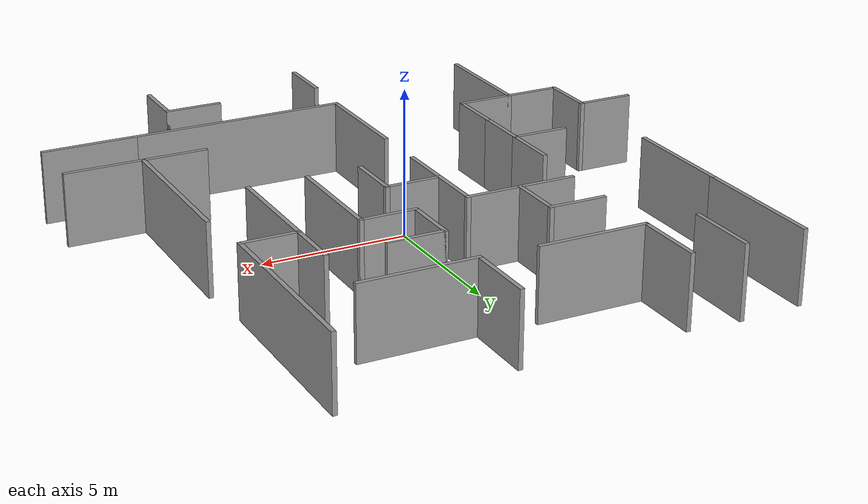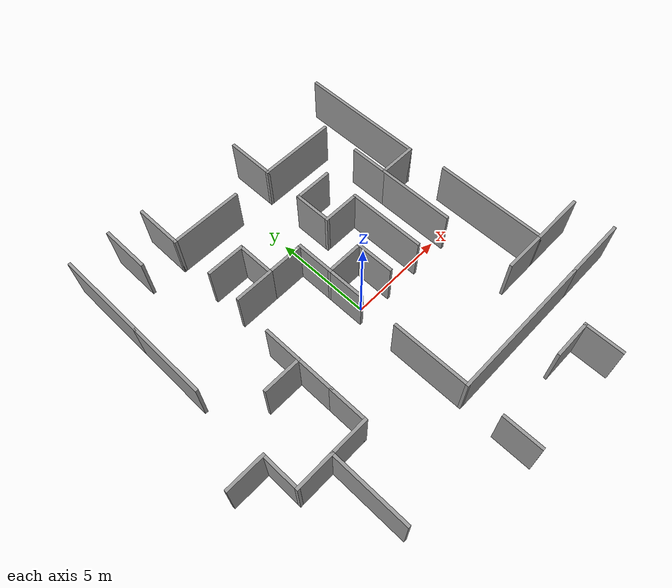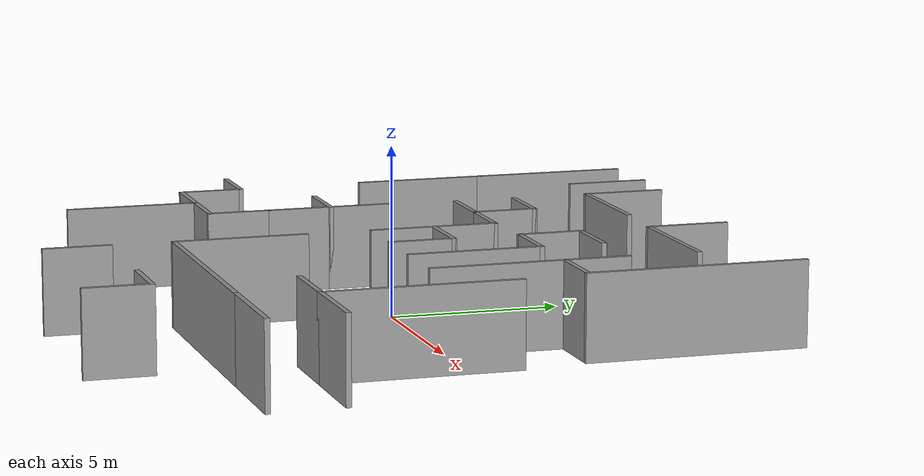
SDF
<?xml version='1.0'?>
<sdf version='1.6'>
  <model name='maze_new'>
    <link name='Wall_104'>
      <pose frame=''>-5.98541 8.7979 0 0 -0 1.5708</pose>
      <self_collide>0</self_collide>
      <kinematic>0</kinematic>
      <visual name='Wall_104_Visual'>
        <pose frame=''>0 0 1.25 0 -0 0</pose>
        <geometry>
          <box>
            <size>2.5 0.15 2.5</size>
          </box>
        </geometry>
        <material>
          <script>
            <uri>file://media/materials/scripts/gazebo.material</uri>
            <name>Gazebo/Grey</name>
          </script>
          <ambient>1 1 1 1</ambient>
          <diffuse>0.7 0.7 0.7 1</diffuse>
          <specular>0.01 0.01 0.01 1</specular>
          <emissive>0 0 0 1</emissive>
        </material>
        <cast_shadows>1</cast_shadows>
        <transparency>0</transparency>
      </visual>
      <collision name='Wall_104_Collision'>
        <laser_retro>0</laser_retro>
        <max_contacts>10</max_contacts>
        <pose frame=''>0 0 1.25 0 -0 0</pose>
        <geometry>
          <box>
            <size>2.5 0.15 2.5</size>
          </box>
        </geometry>
        <surface>
          <friction>
            <ode>
              <mu>1</mu>
              <mu2>1</mu2>
              <fdir1>0 0 0</fdir1>
              <slip1>0</slip1>
              <slip2>0</slip2>
            </ode>
            <torsional>
              <coefficient>1</coefficient>
              <patch_radius>0</patch_radius>
              <surface_radius>0</surface_radius>
              <use_patch_radius>1</use_patch_radius>
              <ode>
                <slip>0</slip>
              </ode>
            </torsional>
          </friction>
          <bounce>
            <restitution_coefficient>0</restitution_coefficient>
            <threshold>1e+06</threshold>
          </bounce>
          <contact>
            <collide_without_contact>0</collide_without_contact>
            <collide_without_contact_bitmask>1</collide_without_contact_bitmask>
            <collide_bitmask>1</collide_bitmask>
            <ode>
              <soft_cfm>0</soft_cfm>
              <soft_erp>0.2</soft_erp>
              <kp>1e+13</kp>
              <kd>1</kd>
              <max_vel>0.01</max_vel>
              <min_depth>0</min_depth>
            </ode>
            <bullet>
              <split_impulse>1</split_impulse>
              <split_impulse_penetration_threshold>-0.01</split_impulse_penetration_threshold>
              <soft_cfm>0</soft_cfm>
              <soft_erp>0.2</soft_erp>
              <kp>1e+13</kp>
              <kd>1</kd>
            </bullet>
          </contact>
        </surface>
      </collision>
    </link>
    <link name='Wall_107'>
      <pose frame=''>-2.4 7.4771 0 0 -0 0</pose>
      <self_collide>0</self_collide>
      <kinematic>0</kinematic>
      <visual name='Wall_107_Visual'>
        <pose frame=''>0 0 1.25 0 -0 0</pose>
        <geometry>
          <box>
            <size>3.75 0.15 2.5</size>
          </box>
        </geometry>
        <material>
          <script>
            <uri>file://media/materials/scripts/gazebo.material</uri>
            <name>Gazebo/Grey</name>
          </script>
          <ambient>1 1 1 1</ambient>
          <diffuse>0.7 0.7 0.7 1</diffuse>
          <specular>0.01 0.01 0.01 1</specular>
          <emissive>0 0 0 1</emissive>
        </material>
        <cast_shadows>1</cast_shadows>
        <transparency>0</transparency>
      </visual>
      <collision name='Wall_107_Collision'>
        <laser_retro>0</laser_retro>
        <max_contacts>10</max_contacts>
        <pose frame=''>0 0 1.25 0 -0 0</pose>
        <geometry>
          <box>
            <size>3.75 0.15 2.5</size>
          </box>
        </geometry>
        <surface>
          <friction>
            <ode>
              <mu>1</mu>
              <mu2>1</mu2>
              <fdir1>0 0 0</fdir1>
              <slip1>0</slip1>
              <slip2>0</slip2>
            </ode>
            <torsional>
              <coefficient>1</coefficient>
              <patch_radius>0</patch_radius>
              <surface_radius>0</surface_radius>
              <use_patch_radius>1</use_patch_radius>
              <ode>
                <slip>0</slip>
              </ode>
            </torsional>
          </friction>
          <bounce>
            <restitution_coefficient>0</restitution_coefficient>
            <threshold>1e+06</threshold>
          </bounce>
          <contact>
            <collide_without_contact>0</collide_without_contact>
            <collide_without_contact_bitmask>1</collide_without_contact_bitmask>
            <collide_bitmask>1</collide_bitmask>
            <ode>
              <soft_cfm>0</soft_cfm>
              <soft_erp>0.2</soft_erp>
              <kp>1e+13</kp>
              <kd>1</kd>
              <max_vel>0.01</max_vel>
              <min_depth>0</min_depth>
            </ode>
            <bullet>
              <split_impulse>1</split_impulse>
              <split_impulse_penetration_threshold>-0.01</split_impulse_penetration_threshold>
              <soft_cfm>0</soft_cfm>
              <soft_erp>0.2</soft_erp>
              <kp>1e+13</kp>
              <kd>1</kd>
            </bullet>
          </contact>
        </surface>
      </collision>
    </link>
    <link name='Wall_11'>
      <pose frame=''>-6.25 -6.22653 0 0 -0 1.5708</pose>
      <self_collide>0</self_collide>
      <kinematic>0</kinematic>
      <visual name='Wall_11_Visual'>
        <pose frame=''>0 0 1.25 0 -0 0</pose>
        <geometry>
          <box>
            <size>4 0.15 2.5</size>
          </box>
        </geometry>
        <material>
          <script>
            <uri>file://media/materials/scripts/gazebo.material</uri>
            <name>Gazebo/Grey</name>
          </script>
          <ambient>1 1 1 1</ambient>
          <diffuse>0.7 0.7 0.7 1</diffuse>
          <specular>0.01 0.01 0.01 1</specular>
          <emissive>0 0 0 1</emissive>
        </material>
        <cast_shadows>1</cast_shadows>
        <transparency>0</transparency>
      </visual>
      <collision name='Wall_11_Collision'>
        <laser_retro>0</laser_retro>
        <max_contacts>10</max_contacts>
        <pose frame=''>0 0 1.25 0 -0 0</pose>
        <geometry>
          <box>
            <size>4 0.15 2.5</size>
          </box>
        </geometry>
        <surface>
          <friction>
            <ode>
              <mu>1</mu>
              <mu2>1</mu2>
              <fdir1>0 0 0</fdir1>
              <slip1>0</slip1>
              <slip2>0</slip2>
            </ode>
            <torsional>
              <coefficient>1</coefficient>
              <patch_radius>0</patch_radius>
              <surface_radius>0</surface_radius>
              <use_patch_radius>1</use_patch_radius>
              <ode>
                <slip>0</slip>
              </ode>
            </torsional>
          </friction>
          <bounce>
            <restitution_coefficient>0</restitution_coefficient>
            <threshold>1e+06</threshold>
          </bounce>
          <contact>
            <collide_without_contact>0</collide_without_contact>
            <collide_without_contact_bitmask>1</collide_without_contact_bitmask>
            <collide_bitmask>1</collide_bitmask>
            <ode>
              <soft_cfm>0</soft_cfm>
              <soft_erp>0.2</soft_erp>
              <kp>1e+13</kp>
              <kd>1</kd>
              <max_vel>0.01</max_vel>
              <min_depth>0</min_depth>
            </ode>
            <bullet>
              <split_impulse>1</split_impulse>
              <split_impulse_penetration_threshold>-0.01</split_impulse_penetration_threshold>
              <soft_cfm>0</soft_cfm>
              <soft_erp>0.2</soft_erp>
              <kp>1e+13</kp>
              <kd>1</kd>
            </bullet>
          </contact>
        </surface>
      </collision>
    </link>
    <link name='Wall_110'>
      <pose frame=''>-4.2 8.6521 0 0 -0 1.5708</pose>
      <self_collide>0</self_collide>
      <kinematic>0</kinematic>
      <visual name='Wall_110_Visual'>
        <pose frame=''>0 0 1.25 0 -0 0</pose>
        <geometry>
          <box>
            <size>2.5 0.15 2.5</size>
          </box>
        </geometry>
        <material>
          <script>
            <uri>file://media/materials/scripts/gazebo.material</uri>
            <name>Gazebo/Grey</name>
          </script>
          <ambient>1 1 1 1</ambient>
          <diffuse>0.7 0.7 0.7 1</diffuse>
          <specular>0.01 0.01 0.01 1</specular>
          <emissive>0 0 0 1</emissive>
        </material>
        <cast_shadows>1</cast_shadows>
        <transparency>0</transparency>
      </visual>
      <collision name='Wall_110_Collision'>
        <laser_retro>0</laser_retro>
        <max_contacts>10</max_contacts>
        <pose frame=''>0 0 1.25 0 -0 0</pose>
        <geometry>
          <box>
            <size>2.5 0.15 2.5</size>
          </box>
        </geometry>
        <surface>
          <friction>
            <ode>
              <mu>1</mu>
              <mu2>1</mu2>
              <fdir1>0 0 0</fdir1>
              <slip1>0</slip1>
              <slip2>0</slip2>
            </ode>
            <torsional>
              <coefficient>1</coefficient>
              <patch_radius>0</patch_radius>
              <surface_radius>0</surface_radius>
              <use_patch_radius>1</use_patch_radius>
              <ode>
                <slip>0</slip>
              </ode>
            </torsional>
          </friction>
          <bounce>
            <restitution_coefficient>0</restitution_coefficient>
            <threshold>1e+06</threshold>
          </bounce>
          <contact>
            <collide_without_contact>0</collide_without_contact>
            <collide_without_contact_bitmask>1</collide_without_contact_bitmask>
            <collide_bitmask>1</collide_bitmask>
            <ode>
              <soft_cfm>0</soft_cfm>
              <soft_erp>0.2</soft_erp>
              <kp>1e+13</kp>
              <kd>1</kd>
              <max_vel>0.01</max_vel>
              <min_depth>0</min_depth>
            </ode>
            <bullet>
              <split_impulse>1</split_impulse>
              <split_impulse_penetration_threshold>-0.01</split_impulse_penetration_threshold>
              <soft_cfm>0</soft_cfm>
              <soft_erp>0.2</soft_erp>
              <kp>1e+13</kp>
              <kd>1</kd>
            </bullet>
          </contact>
        </surface>
      </collision>
    </link>
    <link name='Wall_113'>
      <pose frame=''>3.275 7.3771 0 0 -0 0</pose>
      <self_collide>0</self_collide>
      <kinematic>0</kinematic>
      <visual name='Wall_113_Visual'>
        <pose frame=''>0 0 1.25 0 -0 0</pose>
        <geometry>
          <box>
            <size>4 0.15 2.5</size>
          </box>
        </geometry>
        <material>
          <script>
            <uri>file://media/materials/scripts/gazebo.material</uri>
            <name>Gazebo/Grey</name>
          </script>
          <ambient>1 1 1 1</ambient>
          <diffuse>0.7 0.7 0.7 1</diffuse>
          <specular>0.01 0.01 0.01 1</specular>
          <emissive>0 0 0 1</emissive>
        </material>
        <cast_shadows>1</cast_shadows>
        <transparency>0</transparency>
      </visual>
      <collision name='Wall_113_Collision'>
        <laser_retro>0</laser_retro>
        <max_contacts>10</max_contacts>
        <pose frame=''>0 0 1.25 0 -0 0</pose>
        <geometry>
          <box>
            <size>4 0.15 2.5</size>
          </box>
        </geometry>
        <surface>
          <friction>
            <ode>
              <mu>1</mu>
              <mu2>1</mu2>
              <fdir1>0 0 0</fdir1>
              <slip1>0</slip1>
              <slip2>0</slip2>
            </ode>
            <torsional>
              <coefficient>1</coefficient>
              <patch_radius>0</patch_radius>
              <surface_radius>0</surface_radius>
              <use_patch_radius>1</use_patch_radius>
              <ode>
                <slip>0</slip>
              </ode>
            </torsional>
          </friction>
          <bounce>
            <restitution_coefficient>0</restitution_coefficient>
            <threshold>1e+06</threshold>
          </bounce>
          <contact>
            <collide_without_contact>0</collide_without_contact>
            <collide_without_contact_bitmask>1</collide_without_contact_bitmask>
            <collide_bitmask>1</collide_bitmask>
            <ode>
              <soft_cfm>0</soft_cfm>
              <soft_erp>0.2</soft_erp>
              <kp>1e+13</kp>
              <kd>1</kd>
              <max_vel>0.01</max_vel>
              <min_depth>0</min_depth>
            </ode>
            <bullet>
              <split_impulse>1</split_impulse>
              <split_impulse_penetration_threshold>-0.01</split_impulse_penetration_threshold>
              <soft_cfm>0</soft_cfm>
              <soft_erp>0.2</soft_erp>
              <kp>1e+13</kp>
              <kd>1</kd>
            </bullet>
          </contact>
        </surface>
      </collision>
    </link>
    <link name='Wall_115'>
      <pose frame=''>1.35 8.5521 0 0 -0 1.5708</pose>
      <self_collide>0</self_collide>
      <kinematic>0</kinematic>
      <visual name='Wall_115_Visual'>
        <pose frame=''>0 0 1.25 0 -0 0</pose>
        <geometry>
          <box>
            <size>2.5 0.15 2.5</size>
          </box>
        </geometry>
        <material>
          <script>
            <uri>file://media/materials/scripts/gazebo.material</uri>
            <name>Gazebo/Grey</name>
          </script>
          <ambient>1 1 1 1</ambient>
          <diffuse>0.7 0.7 0.7 1</diffuse>
          <specular>0.01 0.01 0.01 1</specular>
          <emissive>0 0 0 1</emissive>
        </material>
        <cast_shadows>1</cast_shadows>
        <transparency>0</transparency>
      </visual>
      <collision name='Wall_115_Collision'>
        <laser_retro>0</laser_retro>
        <max_contacts>10</max_contacts>
        <pose frame=''>0 0 1.25 0 -0 0</pose>
        <geometry>
          <box>
            <size>2.5 0.15 2.5</size>
          </box>
        </geometry>
        <surface>
          <friction>
            <ode>
              <mu>1</mu>
              <mu2>1</mu2>
              <fdir1>0 0 0</fdir1>
              <slip1>0</slip1>
              <slip2>0</slip2>
            </ode>
            <torsional>
              <coefficient>1</coefficient>
              <patch_radius>0</patch_radius>
              <surface_radius>0</surface_radius>
              <use_patch_radius>1</use_patch_radius>
              <ode>
                <slip>0</slip>
              </ode>
            </torsional>
          </friction>
          <bounce>
            <restitution_coefficient>0</restitution_coefficient>
            <threshold>1e+06</threshold>
          </bounce>
          <contact>
            <collide_without_contact>0</collide_without_contact>
            <collide_without_contact_bitmask>1</collide_without_contact_bitmask>
            <collide_bitmask>1</collide_bitmask>
            <ode>
              <soft_cfm>0</soft_cfm>
              <soft_erp>0.2</soft_erp>
              <kp>1e+13</kp>
              <kd>1</kd>
              <max_vel>0.01</max_vel>
              <min_depth>0</min_depth>
            </ode>
            <bullet>
              <split_impulse>1</split_impulse>
              <split_impulse_penetration_threshold>-0.01</split_impulse_penetration_threshold>
              <soft_cfm>0</soft_cfm>
              <soft_erp>0.2</soft_erp>
              <kp>1e+13</kp>
              <kd>1</kd>
            </bullet>
          </contact>
        </surface>
      </collision>
    </link>
    <link name='Wall_118'>
      <pose frame=''>5.2 4.3521 0 0 0 -1.5708</pose>
      <self_collide>0</self_collide>
      <kinematic>0</kinematic>
      <visual name='Wall_118_Visual'>
        <pose frame=''>0 0 1.25 0 -0 0</pose>
        <geometry>
          <box>
            <size>2 0.15 2.5</size>
          </box>
        </geometry>
        <material>
          <script>
            <uri>file://media/materials/scripts/gazebo.material</uri>
            <name>Gazebo/Grey</name>
          </script>
          <ambient>1 1 1 1</ambient>
          <diffuse>0.7 0.7 0.7 1</diffuse>
          <specular>0.01 0.01 0.01 1</specular>
          <emissive>0 0 0 1</emissive>
        </material>
        <cast_shadows>1</cast_shadows>
        <transparency>0</transparency>
      </visual>
      <collision name='Wall_118_Collision'>
        <laser_retro>0</laser_retro>
        <max_contacts>10</max_contacts>
        <pose frame=''>0 0 1.25 0 -0 0</pose>
        <geometry>
          <box>
            <size>2 0.15 2.5</size>
          </box>
        </geometry>
        <surface>
          <friction>
            <ode>
              <mu>1</mu>
              <mu2>1</mu2>
              <fdir1>0 0 0</fdir1>
              <slip1>0</slip1>
              <slip2>0</slip2>
            </ode>
            <torsional>
              <coefficient>1</coefficient>
              <patch_radius>0</patch_radius>
              <surface_radius>0</surface_radius>
              <use_patch_radius>1</use_patch_radius>
              <ode>
                <slip>0</slip>
              </ode>
            </torsional>
          </friction>
          <bounce>
            <restitution_coefficient>0</restitution_coefficient>
            <threshold>1e+06</threshold>
          </bounce>
          <contact>
            <collide_without_contact>0</collide_without_contact>
            <collide_without_contact_bitmask>1</collide_without_contact_bitmask>
            <collide_bitmask>1</collide_bitmask>
            <ode>
              <soft_cfm>0</soft_cfm>
              <soft_erp>0.2</soft_erp>
              <kp>1e+13</kp>
              <kd>1</kd>
              <max_vel>0.01</max_vel>
              <min_depth>0</min_depth>
            </ode>
            <bullet>
              <split_impulse>1</split_impulse>
              <split_impulse_penetration_threshold>-0.01</split_impulse_penetration_threshold>
              <soft_cfm>0</soft_cfm>
              <soft_erp>0.2</soft_erp>
              <kp>1e+13</kp>
              <kd>1</kd>
            </bullet>
          </contact>
        </surface>
      </collision>
    </link>
    <link name='Wall_119'>
      <pose frame=''>6.125 3.4271 0 0 -0 0</pose>
      <self_collide>0</self_collide>
      <kinematic>0</kinematic>
      <visual name='Wall_119_Visual'>
        <pose frame=''>0 0 1.25 0 -0 0</pose>
        <geometry>
          <box>
            <size>2 0.15 2.5</size>
          </box>
        </geometry>
        <material>
          <script>
            <uri>file://media/materials/scripts/gazebo.material</uri>
            <name>Gazebo/Grey</name>
          </script>
          <ambient>1 1 1 1</ambient>
          <diffuse>0.7 0.7 0.7 1</diffuse>
          <specular>0.01 0.01 0.01 1</specular>
          <emissive>0 0 0 1</emissive>
        </material>
        <cast_shadows>1</cast_shadows>
        <transparency>0</transparency>
      </visual>
      <collision name='Wall_119_Collision'>
        <laser_retro>0</laser_retro>
        <max_contacts>10</max_contacts>
        <pose frame=''>0 0 1.25 0 -0 0</pose>
        <geometry>
          <box>
            <size>2 0.15 2.5</size>
          </box>
        </geometry>
        <surface>
          <friction>
            <ode>
              <mu>1</mu>
              <mu2>1</mu2>
              <fdir1>0 0 0</fdir1>
              <slip1>0</slip1>
              <slip2>0</slip2>
            </ode>
            <torsional>
              <coefficient>1</coefficient>
              <patch_radius>0</patch_radius>
              <surface_radius>0</surface_radius>
              <use_patch_radius>1</use_patch_radius>
              <ode>
                <slip>0</slip>
              </ode>
            </torsional>
          </friction>
          <bounce>
            <restitution_coefficient>0</restitution_coefficient>
            <threshold>1e+06</threshold>
          </bounce>
          <contact>
            <collide_without_contact>0</collide_without_contact>
            <collide_without_contact_bitmask>1</collide_without_contact_bitmask>
            <collide_bitmask>1</collide_bitmask>
            <ode>
              <soft_cfm>0</soft_cfm>
              <soft_erp>0.2</soft_erp>
              <kp>1e+13</kp>
              <kd>1</kd>
              <max_vel>0.01</max_vel>
              <min_depth>0</min_depth>
            </ode>
            <bullet>
              <split_impulse>1</split_impulse>
              <split_impulse_penetration_threshold>-0.01</split_impulse_penetration_threshold>
              <soft_cfm>0</soft_cfm>
              <soft_erp>0.2</soft_erp>
              <kp>1e+13</kp>
              <kd>1</kd>
            </bullet>
          </contact>
        </surface>
      </collision>
    </link>
    <link name='Wall_120'>
      <pose frame=''>7.05 6.6021 0 0 -0 1.5708</pose>
      <self_collide>0</self_collide>
      <kinematic>0</kinematic>
      <visual name='Wall_120_Visual'>
        <pose frame=''>0 0 1.25 0 -0 0</pose>
        <geometry>
          <box>
            <size>6.5 0.15 2.5</size>
          </box>
        </geometry>
        <material>
          <script>
            <uri>file://media/materials/scripts/gazebo.material</uri>
            <name>Gazebo/Grey</name>
          </script>
          <ambient>1 1 1 1</ambient>
          <diffuse>0.7 0.7 0.7 1</diffuse>
          <specular>0.01 0.01 0.01 1</specular>
          <emissive>0 0 0 1</emissive>
        </material>
        <cast_shadows>1</cast_shadows>
        <transparency>0</transparency>
      </visual>
      <collision name='Wall_120_Collision'>
        <laser_retro>0</laser_retro>
        <max_contacts>10</max_contacts>
        <pose frame=''>0 0 1.25 0 -0 0</pose>
        <geometry>
          <box>
            <size>6.5 0.15 2.5</size>
          </box>
        </geometry>
        <surface>
          <friction>
            <ode>
              <mu>1</mu>
              <mu2>1</mu2>
              <fdir1>0 0 0</fdir1>
              <slip1>0</slip1>
              <slip2>0</slip2>
            </ode>
            <torsional>
              <coefficient>1</coefficient>
              <patch_radius>0</patch_radius>
              <surface_radius>0</surface_radius>
              <use_patch_radius>1</use_patch_radius>
              <ode>
                <slip>0</slip>
              </ode>
            </torsional>
          </friction>
          <bounce>
            <restitution_coefficient>0</restitution_coefficient>
            <threshold>1e+06</threshold>
          </bounce>
          <contact>
            <collide_without_contact>0</collide_without_contact>
            <collide_without_contact_bitmask>1</collide_without_contact_bitmask>
            <collide_bitmask>1</collide_bitmask>
            <ode>
              <soft_cfm>0</soft_cfm>
              <soft_erp>0.2</soft_erp>
              <kp>1e+13</kp>
              <kd>1</kd>
              <max_vel>0.01</max_vel>
              <min_depth>0</min_depth>
            </ode>
            <bullet>
              <split_impulse>1</split_impulse>
              <split_impulse_penetration_threshold>-0.01</split_impulse_penetration_threshold>
              <soft_cfm>0</soft_cfm>
              <soft_erp>0.2</soft_erp>
              <kp>1e+13</kp>
              <kd>1</kd>
            </bullet>
          </contact>
        </surface>
      </collision>
    </link>
    <link name='Wall_122'>
      <pose frame=''>5.2 1.5021 0 0 0 -1.5708</pose>
      <self_collide>0</self_collide>
      <kinematic>0</kinematic>
      <visual name='Wall_122_Visual'>
        <pose frame=''>0 0 1.25 0 -0 0</pose>
        <geometry>
          <box>
            <size>4 0.15 2.5</size>
          </box>
        </geometry>
        <material>
          <script>
            <uri>file://media/materials/scripts/gazebo.material</uri>
            <name>Gazebo/Grey</name>
          </script>
          <ambient>1 1 1 1</ambient>
          <diffuse>0.7 0.7 0.7 1</diffuse>
          <specular>0.01 0.01 0.01 1</specular>
          <emissive>0 0 0 1</emissive>
        </material>
        <cast_shadows>1</cast_shadows>
        <transparency>0</transparency>
      </visual>
      <collision name='Wall_122_Collision'>
        <laser_retro>0</laser_retro>
        <max_contacts>10</max_contacts>
        <pose frame=''>0 0 1.25 0 -0 0</pose>
        <geometry>
          <box>
            <size>4 0.15 2.5</size>
          </box>
        </geometry>
        <surface>
          <friction>
            <ode>
              <mu>1</mu>
              <mu2>1</mu2>
              <fdir1>0 0 0</fdir1>
              <slip1>0</slip1>
              <slip2>0</slip2>
            </ode>
            <torsional>
              <coefficient>1</coefficient>
              <patch_radius>0</patch_radius>
              <surface_radius>0</surface_radius>
              <use_patch_radius>1</use_patch_radius>
              <ode>
                <slip>0</slip>
              </ode>
            </torsional>
          </friction>
          <bounce>
            <restitution_coefficient>0</restitution_coefficient>
            <threshold>1e+06</threshold>
          </bounce>
          <contact>
            <collide_without_contact>0</collide_without_contact>
            <collide_without_contact_bitmask>1</collide_without_contact_bitmask>
            <collide_bitmask>1</collide_bitmask>
            <ode>
              <soft_cfm>0</soft_cfm>
              <soft_erp>0.2</soft_erp>
              <kp>1e+13</kp>
              <kd>1</kd>
              <max_vel>0.01</max_vel>
              <min_depth>0</min_depth>
            </ode>
            <bullet>
              <split_impulse>1</split_impulse>
              <split_impulse_penetration_threshold>-0.01</split_impulse_penetration_threshold>
              <soft_cfm>0</soft_cfm>
              <soft_erp>0.2</soft_erp>
              <kp>1e+13</kp>
              <kd>1</kd>
            </bullet>
          </contact>
        </surface>
      </collision>
    </link>
    <link name='Wall_125'>
      <pose frame=''>6.25 -4.1229 0 0 -0 0</pose>
      <self_collide>0</self_collide>
      <kinematic>0</kinematic>
      <visual name='Wall_125_Visual'>
        <pose frame=''>0 0 1.25 0 -0 0</pose>
        <geometry>
          <box>
            <size>2.25 0.15 2.5</size>
          </box>
        </geometry>
        <material>
          <script>
            <uri>file://media/materials/scripts/gazebo.material</uri>
            <name>Gazebo/Grey</name>
          </script>
          <ambient>1 1 1 1</ambient>
          <diffuse>0.7 0.7 0.7 1</diffuse>
          <specular>0.01 0.01 0.01 1</specular>
          <emissive>0 0 0 1</emissive>
        </material>
        <cast_shadows>1</cast_shadows>
        <transparency>0</transparency>
      </visual>
      <collision name='Wall_125_Collision'>
        <laser_retro>0</laser_retro>
        <max_contacts>10</max_contacts>
        <pose frame=''>0 0 1.25 0 -0 0</pose>
        <geometry>
          <box>
            <size>2.25 0.15 2.5</size>
          </box>
        </geometry>
        <surface>
          <friction>
            <ode>
              <mu>1</mu>
              <mu2>1</mu2>
              <fdir1>0 0 0</fdir1>
              <slip1>0</slip1>
              <slip2>0</slip2>
            </ode>
            <torsional>
              <coefficient>1</coefficient>
              <patch_radius>0</patch_radius>
              <surface_radius>0</surface_radius>
              <use_patch_radius>1</use_patch_radius>
              <ode>
                <slip>0</slip>
              </ode>
            </torsional>
          </friction>
          <bounce>
            <restitution_coefficient>0</restitution_coefficient>
            <threshold>1e+06</threshold>
          </bounce>
          <contact>
            <collide_without_contact>0</collide_without_contact>
            <collide_without_contact_bitmask>1</collide_without_contact_bitmask>
            <collide_bitmask>1</collide_bitmask>
            <ode>
              <soft_cfm>0</soft_cfm>
              <soft_erp>0.2</soft_erp>
              <kp>1e+13</kp>
              <kd>1</kd>
              <max_vel>0.01</max_vel>
              <min_depth>0</min_depth>
            </ode>
            <bullet>
              <split_impulse>1</split_impulse>
              <split_impulse_penetration_threshold>-0.01</split_impulse_penetration_threshold>
              <soft_cfm>0</soft_cfm>
              <soft_erp>0.2</soft_erp>
              <kp>1e+13</kp>
              <kd>1</kd>
            </bullet>
          </contact>
        </surface>
      </collision>
    </link>
    <link name='Wall_126'>
      <pose frame=''>7.3 -1.3229 0 0 -0 1.5708</pose>
      <self_collide>0</self_collide>
      <kinematic>0</kinematic>
      <visual name='Wall_126_Visual'>
        <pose frame=''>0 0 1.25 0 -0 0</pose>
        <geometry>
          <box>
            <size>5.75 0.15 2.5</size>
          </box>
        </geometry>
        <material>
          <script>
            <uri>file://media/materials/scripts/gazebo.material</uri>
            <name>Gazebo/Grey</name>
          </script>
          <ambient>1 1 1 1</ambient>
          <diffuse>0.7 0.7 0.7 1</diffuse>
          <specular>0.01 0.01 0.01 1</specular>
          <emissive>0 0 0 1</emissive>
        </material>
        <cast_shadows>1</cast_shadows>
        <transparency>0</transparency>
      </visual>
      <collision name='Wall_126_Collision'>
        <laser_retro>0</laser_retro>
        <max_contacts>10</max_contacts>
        <pose frame=''>0 0 1.25 0 -0 0</pose>
        <geometry>
          <box>
            <size>5.75 0.15 2.5</size>
          </box>
        </geometry>
        <surface>
          <friction>
            <ode>
              <mu>1</mu>
              <mu2>1</mu2>
              <fdir1>0 0 0</fdir1>
              <slip1>0</slip1>
              <slip2>0</slip2>
            </ode>
            <torsional>
              <coefficient>1</coefficient>
              <patch_radius>0</patch_radius>
              <surface_radius>0</surface_radius>
              <use_patch_radius>1</use_patch_radius>
              <ode>
                <slip>0</slip>
              </ode>
            </torsional>
          </friction>
          <bounce>
            <restitution_coefficient>0</restitution_coefficient>
            <threshold>1e+06</threshold>
          </bounce>
          <contact>
            <collide_without_contact>0</collide_without_contact>
            <collide_without_contact_bitmask>1</collide_without_contact_bitmask>
            <collide_bitmask>1</collide_bitmask>
            <ode>
              <soft_cfm>0</soft_cfm>
              <soft_erp>0.2</soft_erp>
              <kp>1e+13</kp>
              <kd>1</kd>
              <max_vel>0.01</max_vel>
              <min_depth>0</min_depth>
            </ode>
            <bullet>
              <split_impulse>1</split_impulse>
              <split_impulse_penetration_threshold>-0.01</split_impulse_penetration_threshold>
              <soft_cfm>0</soft_cfm>
              <soft_erp>0.2</soft_erp>
              <kp>1e+13</kp>
              <kd>1</kd>
            </bullet>
          </contact>
        </surface>
      </collision>
    </link>
    <link name='Wall_128'>
      <pose frame=''>8.6 -4.1229 0 0 -0 0</pose>
      <self_collide>0</self_collide>
      <kinematic>0</kinematic>
      <visual name='Wall_128_Visual'>
        <pose frame=''>0 0 1.25 0 -0 0</pose>
        <geometry>
          <box>
            <size>2.75 0.15 2.5</size>
          </box>
        </geometry>
        <material>
          <script>
            <uri>file://media/materials/scripts/gazebo.material</uri>
            <name>Gazebo/Grey</name>
          </script>
          <ambient>1 1 1 1</ambient>
          <diffuse>0.7 0.7 0.7 1</diffuse>
          <specular>0.01 0.01 0.01 1</specular>
          <emissive>0 0 0 1</emissive>
        </material>
        <cast_shadows>1</cast_shadows>
        <transparency>0</transparency>
      </visual>
      <collision name='Wall_128_Collision'>
        <laser_retro>0</laser_retro>
        <max_contacts>10</max_contacts>
        <pose frame=''>0 0 1.25 0 -0 0</pose>
        <geometry>
          <box>
            <size>2.75 0.15 2.5</size>
          </box>
        </geometry>
        <surface>
          <friction>
            <ode>
              <mu>1</mu>
              <mu2>1</mu2>
              <fdir1>0 0 0</fdir1>
              <slip1>0</slip1>
              <slip2>0</slip2>
            </ode>
            <torsional>
              <coefficient>1</coefficient>
              <patch_radius>0</patch_radius>
              <surface_radius>0</surface_radius>
              <use_patch_radius>1</use_patch_radius>
              <ode>
                <slip>0</slip>
              </ode>
            </torsional>
          </friction>
          <bounce>
            <restitution_coefficient>0</restitution_coefficient>
            <threshold>1e+06</threshold>
          </bounce>
          <contact>
            <collide_without_contact>0</collide_without_contact>
            <collide_without_contact_bitmask>1</collide_without_contact_bitmask>
            <collide_bitmask>1</collide_bitmask>
            <ode>
              <soft_cfm>0</soft_cfm>
              <soft_erp>0.2</soft_erp>
              <kp>1e+13</kp>
              <kd>1</kd>
              <max_vel>0.01</max_vel>
              <min_depth>0</min_depth>
            </ode>
            <bullet>
              <split_impulse>1</split_impulse>
              <split_impulse_penetration_threshold>-0.01</split_impulse_penetration_threshold>
              <soft_cfm>0</soft_cfm>
              <soft_erp>0.2</soft_erp>
              <kp>1e+13</kp>
              <kd>1</kd>
            </bullet>
          </contact>
        </surface>
      </collision>
    </link>
    <link name='Wall_13'>
      <pose frame=''>-7.175 -4.30153 0 0 -0 3.14159</pose>
      <self_collide>0</self_collide>
      <kinematic>0</kinematic>
      <visual name='Wall_13_Visual'>
        <pose frame=''>0 0 1.25 0 -0 0</pose>
        <geometry>
          <box>
            <size>2 0.15 2.5</size>
          </box>
        </geometry>
        <material>
          <script>
            <uri>file://media/materials/scripts/gazebo.material</uri>
            <name>Gazebo/Grey</name>
          </script>
          <ambient>1 1 1 1</ambient>
          <diffuse>0.7 0.7 0.7 1</diffuse>
          <specular>0.01 0.01 0.01 1</specular>
          <emissive>0 0 0 1</emissive>
        </material>
        <cast_shadows>1</cast_shadows>
        <transparency>0</transparency>
      </visual>
      <collision name='Wall_13_Collision'>
        <laser_retro>0</laser_retro>
        <max_contacts>10</max_contacts>
        <pose frame=''>0 0 1.25 0 -0 0</pose>
        <geometry>
          <box>
            <size>2 0.15 2.5</size>
          </box>
        </geometry>
        <surface>
          <friction>
            <ode>
              <mu>1</mu>
              <mu2>1</mu2>
              <fdir1>0 0 0</fdir1>
              <slip1>0</slip1>
              <slip2>0</slip2>
            </ode>
            <torsional>
              <coefficient>1</coefficient>
              <patch_radius>0</patch_radius>
              <surface_radius>0</surface_radius>
              <use_patch_radius>1</use_patch_radius>
              <ode>
                <slip>0</slip>
              </ode>
            </torsional>
          </friction>
          <bounce>
            <restitution_coefficient>0</restitution_coefficient>
            <threshold>1e+06</threshold>
          </bounce>
          <contact>
            <collide_without_contact>0</collide_without_contact>
            <collide_without_contact_bitmask>1</collide_without_contact_bitmask>
            <collide_bitmask>1</collide_bitmask>
            <ode>
              <soft_cfm>0</soft_cfm>
              <soft_erp>0.2</soft_erp>
              <kp>1e+13</kp>
              <kd>1</kd>
              <max_vel>0.01</max_vel>
              <min_depth>0</min_depth>
            </ode>
            <bullet>
              <split_impulse>1</split_impulse>
              <split_impulse_penetration_threshold>-0.01</split_impulse_penetration_threshold>
              <soft_cfm>0</soft_cfm>
              <soft_erp>0.2</soft_erp>
              <kp>1e+13</kp>
              <kd>1</kd>
            </bullet>
          </contact>
        </surface>
      </collision>
    </link>
    <link name='Wall_14'>
      <pose frame=''>-8.1 -3.37653 0 0 -0 1.5708</pose>
      <self_collide>0</self_collide>
      <kinematic>0</kinematic>
      <visual name='Wall_14_Visual'>
        <pose frame=''>0 0 1.25 0 -0 0</pose>
        <geometry>
          <box>
            <size>2 0.15 2.5</size>
          </box>
        </geometry>
        <material>
          <script>
            <uri>file://media/materials/scripts/gazebo.material</uri>
            <name>Gazebo/Grey</name>
          </script>
          <ambient>1 1 1 1</ambient>
          <diffuse>0.7 0.7 0.7 1</diffuse>
          <specular>0.01 0.01 0.01 1</specular>
          <emissive>0 0 0 1</emissive>
        </material>
        <cast_shadows>1</cast_shadows>
        <transparency>0</transparency>
      </visual>
      <collision name='Wall_14_Collision'>
        <laser_retro>0</laser_retro>
        <max_contacts>10</max_contacts>
        <pose frame=''>0 0 1.25 0 -0 0</pose>
        <geometry>
          <box>
            <size>2 0.15 2.5</size>
          </box>
        </geometry>
        <surface>
          <friction>
            <ode>
              <mu>1</mu>
              <mu2>1</mu2>
              <fdir1>0 0 0</fdir1>
              <slip1>0</slip1>
              <slip2>0</slip2>
            </ode>
            <torsional>
              <coefficient>1</coefficient>
              <patch_radius>0</patch_radius>
              <surface_radius>0</surface_radius>
              <use_patch_radius>1</use_patch_radius>
              <ode>
                <slip>0</slip>
              </ode>
            </torsional>
          </friction>
          <bounce>
            <restitution_coefficient>0</restitution_coefficient>
            <threshold>1e+06</threshold>
          </bounce>
          <contact>
            <collide_without_contact>0</collide_without_contact>
            <collide_without_contact_bitmask>1</collide_without_contact_bitmask>
            <collide_bitmask>1</collide_bitmask>
            <ode>
              <soft_cfm>0</soft_cfm>
              <soft_erp>0.2</soft_erp>
              <kp>1e+13</kp>
              <kd>1</kd>
              <max_vel>0.01</max_vel>
              <min_depth>0</min_depth>
            </ode>
            <bullet>
              <split_impulse>1</split_impulse>
              <split_impulse_penetration_threshold>-0.01</split_impulse_penetration_threshold>
              <soft_cfm>0</soft_cfm>
              <soft_erp>0.2</soft_erp>
              <kp>1e+13</kp>
              <kd>1</kd>
            </bullet>
          </contact>
        </surface>
      </collision>
    </link>
    <link name='Wall_15'>
      <pose frame=''>-9.025 -2.45153 0 0 -0 3.14159</pose>
      <self_collide>0</self_collide>
      <kinematic>0</kinematic>
      <visual name='Wall_15_Visual'>
        <pose frame=''>0 0 1.25 0 -0 0</pose>
        <geometry>
          <box>
            <size>2 0.15 2.5</size>
          </box>
        </geometry>
        <material>
          <script>
            <uri>file://media/materials/scripts/gazebo.material</uri>
            <name>Gazebo/Grey</name>
          </script>
          <ambient>1 1 1 1</ambient>
          <diffuse>0.7 0.7 0.7 1</diffuse>
          <specular>0.01 0.01 0.01 1</specular>
          <emissive>0 0 0 1</emissive>
        </material>
        <cast_shadows>1</cast_shadows>
        <transparency>0</transparency>
      </visual>
      <collision name='Wall_15_Collision'>
        <laser_retro>0</laser_retro>
        <max_contacts>10</max_contacts>
        <pose frame=''>0 0 1.25 0 -0 0</pose>
        <geometry>
          <box>
            <size>2 0.15 2.5</size>
          </box>
        </geometry>
        <surface>
          <friction>
            <ode>
              <mu>1</mu>
              <mu2>1</mu2>
              <fdir1>0 0 0</fdir1>
              <slip1>0</slip1>
              <slip2>0</slip2>
            </ode>
            <torsional>
              <coefficient>1</coefficient>
              <patch_radius>0</patch_radius>
              <surface_radius>0</surface_radius>
              <use_patch_radius>1</use_patch_radius>
              <ode>
                <slip>0</slip>
              </ode>
            </torsional>
          </friction>
          <bounce>
            <restitution_coefficient>0</restitution_coefficient>
            <threshold>1e+06</threshold>
          </bounce>
          <contact>
            <collide_without_contact>0</collide_without_contact>
            <collide_without_contact_bitmask>1</collide_without_contact_bitmask>
            <collide_bitmask>1</collide_bitmask>
            <ode>
              <soft_cfm>0</soft_cfm>
              <soft_erp>0.2</soft_erp>
              <kp>1e+13</kp>
              <kd>1</kd>
              <max_vel>0.01</max_vel>
              <min_depth>0</min_depth>
            </ode>
            <bullet>
              <split_impulse>1</split_impulse>
              <split_impulse_penetration_threshold>-0.01</split_impulse_penetration_threshold>
              <soft_cfm>0</soft_cfm>
              <soft_erp>0.2</soft_erp>
              <kp>1e+13</kp>
              <kd>1</kd>
            </bullet>
          </contact>
        </surface>
      </collision>
    </link>
    <link name='Wall_19'>
      <pose frame=''>-5.325 -4.30153 0 0 -0 0</pose>
      <self_collide>0</self_collide>
      <kinematic>0</kinematic>
      <visual name='Wall_19_Visual'>
        <pose frame=''>0 0 1.25 0 -0 0</pose>
        <geometry>
          <box>
            <size>2 0.15 2.5</size>
          </box>
        </geometry>
        <material>
          <script>
            <uri>file://media/materials/scripts/gazebo.material</uri>
            <name>Gazebo/Grey</name>
          </script>
          <ambient>1 1 1 1</ambient>
          <diffuse>0.7 0.7 0.7 1</diffuse>
          <specular>0.01 0.01 0.01 1</specular>
          <emissive>0 0 0 1</emissive>
        </material>
        <cast_shadows>1</cast_shadows>
        <transparency>0</transparency>
      </visual>
      <collision name='Wall_19_Collision'>
        <laser_retro>0</laser_retro>
        <max_contacts>10</max_contacts>
        <pose frame=''>0 0 1.25 0 -0 0</pose>
        <geometry>
          <box>
            <size>2 0.15 2.5</size>
          </box>
        </geometry>
        <surface>
          <friction>
            <ode>
              <mu>1</mu>
              <mu2>1</mu2>
              <fdir1>0 0 0</fdir1>
              <slip1>0</slip1>
              <slip2>0</slip2>
            </ode>
            <torsional>
              <coefficient>1</coefficient>
              <patch_radius>0</patch_radius>
              <surface_radius>0</surface_radius>
              <use_patch_radius>1</use_patch_radius>
              <ode>
                <slip>0</slip>
              </ode>
            </torsional>
          </friction>
          <bounce>
            <restitution_coefficient>0</restitution_coefficient>
            <threshold>1e+06</threshold>
          </bounce>
          <contact>
            <collide_without_contact>0</collide_without_contact>
            <collide_without_contact_bitmask>1</collide_without_contact_bitmask>
            <collide_bitmask>1</collide_bitmask>
            <ode>
              <soft_cfm>0</soft_cfm>
              <soft_erp>0.2</soft_erp>
              <kp>1e+13</kp>
              <kd>1</kd>
              <max_vel>0.01</max_vel>
              <min_depth>0</min_depth>
            </ode>
            <bullet>
              <split_impulse>1</split_impulse>
              <split_impulse_penetration_threshold>-0.01</split_impulse_penetration_threshold>
              <soft_cfm>0</soft_cfm>
              <soft_erp>0.2</soft_erp>
              <kp>1e+13</kp>
              <kd>1</kd>
            </bullet>
          </contact>
        </surface>
      </collision>
    </link>
    <link name='Wall_20'>
      <pose frame=''>-4.4 -3.37653 0 0 -0 1.5708</pose>
      <self_collide>0</self_collide>
      <kinematic>0</kinematic>
      <visual name='Wall_20_Visual'>
        <pose frame=''>0 0 1.25 0 -0 0</pose>
        <geometry>
          <box>
            <size>2 0.15 2.5</size>
          </box>
        </geometry>
        <material>
          <script>
            <uri>file://media/materials/scripts/gazebo.material</uri>
            <name>Gazebo/Grey</name>
          </script>
          <ambient>1 1 1 1</ambient>
          <diffuse>0.7 0.7 0.7 1</diffuse>
          <specular>0.01 0.01 0.01 1</specular>
          <emissive>0 0 0 1</emissive>
        </material>
        <cast_shadows>1</cast_shadows>
        <transparency>0</transparency>
      </visual>
      <collision name='Wall_20_Collision'>
        <laser_retro>0</laser_retro>
        <max_contacts>10</max_contacts>
        <pose frame=''>0 0 1.25 0 -0 0</pose>
        <geometry>
          <box>
            <size>2 0.15 2.5</size>
          </box>
        </geometry>
        <surface>
          <friction>
            <ode>
              <mu>1</mu>
              <mu2>1</mu2>
              <fdir1>0 0 0</fdir1>
              <slip1>0</slip1>
              <slip2>0</slip2>
            </ode>
            <torsional>
              <coefficient>1</coefficient>
              <patch_radius>0</patch_radius>
              <surface_radius>0</surface_radius>
              <use_patch_radius>1</use_patch_radius>
              <ode>
                <slip>0</slip>
              </ode>
            </torsional>
          </friction>
          <bounce>
            <restitution_coefficient>0</restitution_coefficient>
            <threshold>1e+06</threshold>
          </bounce>
          <contact>
            <collide_without_contact>0</collide_without_contact>
            <collide_without_contact_bitmask>1</collide_without_contact_bitmask>
            <collide_bitmask>1</collide_bitmask>
            <ode>
              <soft_cfm>0</soft_cfm>
              <soft_erp>0.2</soft_erp>
              <kp>1e+13</kp>
              <kd>1</kd>
              <max_vel>0.01</max_vel>
              <min_depth>0</min_depth>
            </ode>
            <bullet>
              <split_impulse>1</split_impulse>
              <split_impulse_penetration_threshold>-0.01</split_impulse_penetration_threshold>
              <soft_cfm>0</soft_cfm>
              <soft_erp>0.2</soft_erp>
              <kp>1e+13</kp>
              <kd>1</kd>
            </bullet>
          </contact>
        </surface>
      </collision>
    </link>
    <link name='Wall_28'>
      <pose frame=''>-0.55 -9.0479 0 0 0 -1.5708</pose>
      <self_collide>0</self_collide>
      <kinematic>0</kinematic>
      <visual name='Wall_28_Visual'>
        <pose frame=''>0 0 1.25 0 -0 0</pose>
        <geometry>
          <box>
            <size>2 0.15 2.5</size>
          </box>
        </geometry>
        <material>
          <script>
            <uri>file://media/materials/scripts/gazebo.material</uri>
            <name>Gazebo/Grey</name>
          </script>
          <ambient>1 1 1 1</ambient>
          <diffuse>0.7 0.7 0.7 1</diffuse>
          <specular>0.01 0.01 0.01 1</specular>
          <emissive>0 0 0 1</emissive>
        </material>
        <cast_shadows>1</cast_shadows>
        <transparency>0</transparency>
      </visual>
      <collision name='Wall_28_Collision'>
        <laser_retro>0</laser_retro>
        <max_contacts>10</max_contacts>
        <pose frame=''>0 0 1.25 0 -0 0</pose>
        <geometry>
          <box>
            <size>2 0.15 2.5</size>
          </box>
        </geometry>
        <surface>
          <friction>
            <ode>
              <mu>1</mu>
              <mu2>1</mu2>
              <fdir1>0 0 0</fdir1>
              <slip1>0</slip1>
              <slip2>0</slip2>
            </ode>
            <torsional>
              <coefficient>1</coefficient>
              <patch_radius>0</patch_radius>
              <surface_radius>0</surface_radius>
              <use_patch_radius>1</use_patch_radius>
              <ode>
                <slip>0</slip>
              </ode>
            </torsional>
          </friction>
          <bounce>
            <restitution_coefficient>0</restitution_coefficient>
            <threshold>1e+06</threshold>
          </bounce>
          <contact>
            <collide_without_contact>0</collide_without_contact>
            <collide_without_contact_bitmask>1</collide_without_contact_bitmask>
            <collide_bitmask>1</collide_bitmask>
            <ode>
              <soft_cfm>0</soft_cfm>
              <soft_erp>0.2</soft_erp>
              <kp>1e+13</kp>
              <kd>1</kd>
              <max_vel>0.01</max_vel>
              <min_depth>0</min_depth>
            </ode>
            <bullet>
              <split_impulse>1</split_impulse>
              <split_impulse_penetration_threshold>-0.01</split_impulse_penetration_threshold>
              <soft_cfm>0</soft_cfm>
              <soft_erp>0.2</soft_erp>
              <kp>1e+13</kp>
              <kd>1</kd>
            </bullet>
          </contact>
        </surface>
      </collision>
    </link>
    <link name='Wall_38'>
      <pose frame=''>-4.4 -1.52653 0 0 -0 1.5708</pose>
      <self_collide>0</self_collide>
      <kinematic>0</kinematic>
      <visual name='Wall_38_Visual'>
        <pose frame=''>0 0 1.25 0 -0 0</pose>
        <geometry>
          <box>
            <size>2 0.15 2.5</size>
          </box>
        </geometry>
        <material>
          <script>
            <uri>file://media/materials/scripts/gazebo.material</uri>
            <name>Gazebo/Grey</name>
          </script>
          <ambient>1 1 1 1</ambient>
          <diffuse>0.7 0.7 0.7 1</diffuse>
          <specular>0.01 0.01 0.01 1</specular>
          <emissive>0 0 0 1</emissive>
        </material>
        <cast_shadows>1</cast_shadows>
        <transparency>0</transparency>
      </visual>
      <collision name='Wall_38_Collision'>
        <laser_retro>0</laser_retro>
        <max_contacts>10</max_contacts>
        <pose frame=''>0 0 1.25 0 -0 0</pose>
        <geometry>
          <box>
            <size>2 0.15 2.5</size>
          </box>
        </geometry>
        <surface>
          <friction>
            <ode>
              <mu>1</mu>
              <mu2>1</mu2>
              <fdir1>0 0 0</fdir1>
              <slip1>0</slip1>
              <slip2>0</slip2>
            </ode>
            <torsional>
              <coefficient>1</coefficient>
              <patch_radius>0</patch_radius>
              <surface_radius>0</surface_radius>
              <use_patch_radius>1</use_patch_radius>
              <ode>
                <slip>0</slip>
              </ode>
            </torsional>
          </friction>
          <bounce>
            <restitution_coefficient>0</restitution_coefficient>
            <threshold>1e+06</threshold>
          </bounce>
          <contact>
            <collide_without_contact>0</collide_without_contact>
            <collide_without_contact_bitmask>1</collide_without_contact_bitmask>
            <collide_bitmask>1</collide_bitmask>
            <ode>
              <soft_cfm>0</soft_cfm>
              <soft_erp>0.2</soft_erp>
              <kp>1e+13</kp>
              <kd>1</kd>
              <max_vel>0.01</max_vel>
              <min_depth>0</min_depth>
            </ode>
            <bullet>
              <split_impulse>1</split_impulse>
              <split_impulse_penetration_threshold>-0.01</split_impulse_penetration_threshold>
              <soft_cfm>0</soft_cfm>
              <soft_erp>0.2</soft_erp>
              <kp>1e+13</kp>
              <kd>1</kd>
            </bullet>
          </contact>
        </surface>
      </collision>
    </link>
    <link name='Wall_40'>
      <pose frame=''>-4.4 0.32347 0 0 -0 1.5708</pose>
      <self_collide>0</self_collide>
      <kinematic>0</kinematic>
      <visual name='Wall_40_Visual'>
        <pose frame=''>0 0 1.25 0 -0 0</pose>
        <geometry>
          <box>
            <size>2 0.15 2.5</size>
          </box>
        </geometry>
        <material>
          <script>
            <uri>file://media/materials/scripts/gazebo.material</uri>
            <name>Gazebo/Grey</name>
          </script>
          <ambient>1 1 1 1</ambient>
          <diffuse>0.7 0.7 0.7 1</diffuse>
          <specular>0.01 0.01 0.01 1</specular>
          <emissive>0 0 0 1</emissive>
        </material>
        <cast_shadows>1</cast_shadows>
        <transparency>0</transparency>
      </visual>
      <collision name='Wall_40_Collision'>
        <laser_retro>0</laser_retro>
        <max_contacts>10</max_contacts>
        <pose frame=''>0 0 1.25 0 -0 0</pose>
        <geometry>
          <box>
            <size>2 0.15 2.5</size>
          </box>
        </geometry>
        <surface>
          <friction>
            <ode>
              <mu>1</mu>
              <mu2>1</mu2>
              <fdir1>0 0 0</fdir1>
              <slip1>0</slip1>
              <slip2>0</slip2>
            </ode>
            <torsional>
              <coefficient>1</coefficient>
              <patch_radius>0</patch_radius>
              <surface_radius>0</surface_radius>
              <use_patch_radius>1</use_patch_radius>
              <ode>
                <slip>0</slip>
              </ode>
            </torsional>
          </friction>
          <bounce>
            <restitution_coefficient>0</restitution_coefficient>
            <threshold>1e+06</threshold>
          </bounce>
          <contact>
            <collide_without_contact>0</collide_without_contact>
            <collide_without_contact_bitmask>1</collide_without_contact_bitmask>
            <collide_bitmask>1</collide_bitmask>
            <ode>
              <soft_cfm>0</soft_cfm>
              <soft_erp>0.2</soft_erp>
              <kp>1e+13</kp>
              <kd>1</kd>
              <max_vel>0.01</max_vel>
              <min_depth>0</min_depth>
            </ode>
            <bullet>
              <split_impulse>1</split_impulse>
              <split_impulse_penetration_threshold>-0.01</split_impulse_penetration_threshold>
              <soft_cfm>0</soft_cfm>
              <soft_erp>0.2</soft_erp>
              <kp>1e+13</kp>
              <kd>1</kd>
            </bullet>
          </contact>
        </surface>
      </collision>
    </link>
    <link name='Wall_42'>
      <pose frame=''>-5.325 -0.60153 0 0 -0 3.14159</pose>
      <self_collide>0</self_collide>
      <kinematic>0</kinematic>
      <visual name='Wall_42_Visual'>
        <pose frame=''>0 0 1.25 0 -0 0</pose>
        <geometry>
          <box>
            <size>2 0.15 2.5</size>
          </box>
        </geometry>
        <material>
          <script>
            <uri>file://media/materials/scripts/gazebo.material</uri>
            <name>Gazebo/Grey</name>
          </script>
          <ambient>1 1 1 1</ambient>
          <diffuse>0.7 0.7 0.7 1</diffuse>
          <specular>0.01 0.01 0.01 1</specular>
          <emissive>0 0 0 1</emissive>
        </material>
        <cast_shadows>1</cast_shadows>
        <transparency>0</transparency>
      </visual>
      <collision name='Wall_42_Collision'>
        <laser_retro>0</laser_retro>
        <max_contacts>10</max_contacts>
        <pose frame=''>0 0 1.25 0 -0 0</pose>
        <geometry>
          <box>
            <size>2 0.15 2.5</size>
          </box>
        </geometry>
        <surface>
          <friction>
            <ode>
              <mu>1</mu>
              <mu2>1</mu2>
              <fdir1>0 0 0</fdir1>
              <slip1>0</slip1>
              <slip2>0</slip2>
            </ode>
            <torsional>
              <coefficient>1</coefficient>
              <patch_radius>0</patch_radius>
              <surface_radius>0</surface_radius>
              <use_patch_radius>1</use_patch_radius>
              <ode>
                <slip>0</slip>
              </ode>
            </torsional>
          </friction>
          <bounce>
            <restitution_coefficient>0</restitution_coefficient>
            <threshold>1e+06</threshold>
          </bounce>
          <contact>
            <collide_without_contact>0</collide_without_contact>
            <collide_without_contact_bitmask>1</collide_without_contact_bitmask>
            <collide_bitmask>1</collide_bitmask>
            <ode>
              <soft_cfm>0</soft_cfm>
              <soft_erp>0.2</soft_erp>
              <kp>1e+13</kp>
              <kd>1</kd>
              <max_vel>0.01</max_vel>
              <min_depth>0</min_depth>
            </ode>
            <bullet>
              <split_impulse>1</split_impulse>
              <split_impulse_penetration_threshold>-0.01</split_impulse_penetration_threshold>
              <soft_cfm>0</soft_cfm>
              <soft_erp>0.2</soft_erp>
              <kp>1e+13</kp>
              <kd>1</kd>
            </bullet>
          </contact>
        </surface>
      </collision>
    </link>
    <link name='Wall_50'>
      <pose frame=''>4.075 -8.1229 0 0 -0 0</pose>
      <self_collide>0</self_collide>
      <kinematic>0</kinematic>
      <visual name='Wall_50_Visual'>
        <pose frame=''>0 0 1.25 0 -0 0</pose>
        <geometry>
          <box>
            <size>2 0.15 2.5</size>
          </box>
        </geometry>
        <material>
          <script>
            <uri>file://media/materials/scripts/gazebo.material</uri>
            <name>Gazebo/Grey</name>
          </script>
          <ambient>1 1 1 1</ambient>
          <diffuse>0.7 0.7 0.7 1</diffuse>
          <specular>0.01 0.01 0.01 1</specular>
          <emissive>0 0 0 1</emissive>
        </material>
        <cast_shadows>1</cast_shadows>
        <transparency>0</transparency>
      </visual>
      <collision name='Wall_50_Collision'>
        <laser_retro>0</laser_retro>
        <max_contacts>10</max_contacts>
        <pose frame=''>0 0 1.25 0 -0 0</pose>
        <geometry>
          <box>
            <size>2 0.15 2.5</size>
          </box>
        </geometry>
        <surface>
          <friction>
            <ode>
              <mu>1</mu>
              <mu2>1</mu2>
              <fdir1>0 0 0</fdir1>
              <slip1>0</slip1>
              <slip2>0</slip2>
            </ode>
            <torsional>
              <coefficient>1</coefficient>
              <patch_radius>0</patch_radius>
              <surface_radius>0</surface_radius>
              <use_patch_radius>1</use_patch_radius>
              <ode>
                <slip>0</slip>
              </ode>
            </torsional>
          </friction>
          <bounce>
            <restitution_coefficient>0</restitution_coefficient>
            <threshold>1e+06</threshold>
          </bounce>
          <contact>
            <collide_without_contact>0</collide_without_contact>
            <collide_without_contact_bitmask>1</collide_without_contact_bitmask>
            <collide_bitmask>1</collide_bitmask>
            <ode>
              <soft_cfm>0</soft_cfm>
              <soft_erp>0.2</soft_erp>
              <kp>1e+13</kp>
              <kd>1</kd>
              <max_vel>0.01</max_vel>
              <min_depth>0</min_depth>
            </ode>
            <bullet>
              <split_impulse>1</split_impulse>
              <split_impulse_penetration_threshold>-0.01</split_impulse_penetration_threshold>
              <soft_cfm>0</soft_cfm>
              <soft_erp>0.2</soft_erp>
              <kp>1e+13</kp>
              <kd>1</kd>
            </bullet>
          </contact>
        </surface>
      </collision>
    </link>
    <link name='Wall_51'>
      <pose frame=''>5 -9.0479 0 0 0 -1.5708</pose>
      <self_collide>0</self_collide>
      <kinematic>0</kinematic>
      <visual name='Wall_51_Visual'>
        <pose frame=''>0 0 1.25 0 -0 0</pose>
        <geometry>
          <box>
            <size>2 0.15 2.5</size>
          </box>
        </geometry>
        <material>
          <script>
            <uri>file://media/materials/scripts/gazebo.material</uri>
            <name>Gazebo/Grey</name>
          </script>
          <ambient>1 1 1 1</ambient>
          <diffuse>0.7 0.7 0.7 1</diffuse>
          <specular>0.01 0.01 0.01 1</specular>
          <emissive>0 0 0 1</emissive>
        </material>
        <cast_shadows>1</cast_shadows>
        <transparency>0</transparency>
      </visual>
      <collision name='Wall_51_Collision'>
        <laser_retro>0</laser_retro>
        <max_contacts>10</max_contacts>
        <pose frame=''>0 0 1.25 0 -0 0</pose>
        <geometry>
          <box>
            <size>2 0.15 2.5</size>
          </box>
        </geometry>
        <surface>
          <friction>
            <ode>
              <mu>1</mu>
              <mu2>1</mu2>
              <fdir1>0 0 0</fdir1>
              <slip1>0</slip1>
              <slip2>0</slip2>
            </ode>
            <torsional>
              <coefficient>1</coefficient>
              <patch_radius>0</patch_radius>
              <surface_radius>0</surface_radius>
              <use_patch_radius>1</use_patch_radius>
              <ode>
                <slip>0</slip>
              </ode>
            </torsional>
          </friction>
          <bounce>
            <restitution_coefficient>0</restitution_coefficient>
            <threshold>1e+06</threshold>
          </bounce>
          <contact>
            <collide_without_contact>0</collide_without_contact>
            <collide_without_contact_bitmask>1</collide_without_contact_bitmask>
            <collide_bitmask>1</collide_bitmask>
            <ode>
              <soft_cfm>0</soft_cfm>
              <soft_erp>0.2</soft_erp>
              <kp>1e+13</kp>
              <kd>1</kd>
              <max_vel>0.01</max_vel>
              <min_depth>0</min_depth>
            </ode>
            <bullet>
              <split_impulse>1</split_impulse>
              <split_impulse_penetration_threshold>-0.01</split_impulse_penetration_threshold>
              <soft_cfm>0</soft_cfm>
              <soft_erp>0.2</soft_erp>
              <kp>1e+13</kp>
              <kd>1</kd>
            </bullet>
          </contact>
        </surface>
      </collision>
    </link>
    <link name='Wall_59'>
      <pose frame=''>8.4 -6.2729 0 0 -0 0</pose>
      <self_collide>0</self_collide>
      <kinematic>0</kinematic>
      <visual name='Wall_59_Visual'>
        <pose frame=''>0 0 1.25 0 -0 0</pose>
        <geometry>
          <box>
            <size>3.25 0.15 2.5</size>
          </box>
        </geometry>
        <material>
          <script>
            <uri>file://media/materials/scripts/gazebo.material</uri>
            <name>Gazebo/Grey</name>
          </script>
          <ambient>1 1 1 1</ambient>
          <diffuse>0.7 0.7 0.7 1</diffuse>
          <specular>0.01 0.01 0.01 1</specular>
          <emissive>0 0 0 1</emissive>
        </material>
        <cast_shadows>1</cast_shadows>
        <transparency>0</transparency>
      </visual>
      <collision name='Wall_59_Collision'>
        <laser_retro>0</laser_retro>
        <max_contacts>10</max_contacts>
        <pose frame=''>0 0 1.25 0 -0 0</pose>
        <geometry>
          <box>
            <size>3.25 0.15 2.5</size>
          </box>
        </geometry>
        <surface>
          <friction>
            <ode>
              <mu>1</mu>
              <mu2>1</mu2>
              <fdir1>0 0 0</fdir1>
              <slip1>0</slip1>
              <slip2>0</slip2>
            </ode>
            <torsional>
              <coefficient>1</coefficient>
              <patch_radius>0</patch_radius>
              <surface_radius>0</surface_radius>
              <use_patch_radius>1</use_patch_radius>
              <ode>
                <slip>0</slip>
              </ode>
            </torsional>
          </friction>
          <bounce>
            <restitution_coefficient>0</restitution_coefficient>
            <threshold>1e+06</threshold>
          </bounce>
          <contact>
            <collide_without_contact>0</collide_without_contact>
            <collide_without_contact_bitmask>1</collide_without_contact_bitmask>
            <collide_bitmask>1</collide_bitmask>
            <ode>
              <soft_cfm>0</soft_cfm>
              <soft_erp>0.2</soft_erp>
              <kp>1e+13</kp>
              <kd>1</kd>
              <max_vel>0.01</max_vel>
              <min_depth>0</min_depth>
            </ode>
            <bullet>
              <split_impulse>1</split_impulse>
              <split_impulse_penetration_threshold>-0.01</split_impulse_penetration_threshold>
              <soft_cfm>0</soft_cfm>
              <soft_erp>0.2</soft_erp>
              <kp>1e+13</kp>
              <kd>1</kd>
            </bullet>
          </contact>
        </surface>
      </collision>
    </link>
    <link name='Wall_61'>
      <pose frame=''>3.175 -6.2729 0 0 -0 3.14159</pose>
      <self_collide>0</self_collide>
      <kinematic>0</kinematic>
      <visual name='Wall_61_Visual'>
        <pose frame=''>0 0 1.25 0 -0 0</pose>
        <geometry>
          <box>
            <size>7.5 0.15 2.5</size>
          </box>
        </geometry>
        <material>
          <script>
            <uri>file://media/materials/scripts/gazebo.material</uri>
            <name>Gazebo/Grey</name>
          </script>
          <ambient>1 1 1 1</ambient>
          <diffuse>0.7 0.7 0.7 1</diffuse>
          <specular>0.01 0.01 0.01 1</specular>
          <emissive>0 0 0 1</emissive>
        </material>
        <cast_shadows>1</cast_shadows>
        <transparency>0</transparency>
      </visual>
      <collision name='Wall_61_Collision'>
        <laser_retro>0</laser_retro>
        <max_contacts>10</max_contacts>
        <pose frame=''>0 0 1.25 0 -0 0</pose>
        <geometry>
          <box>
            <size>7.5 0.15 2.5</size>
          </box>
        </geometry>
        <surface>
          <friction>
            <ode>
              <mu>1</mu>
              <mu2>1</mu2>
              <fdir1>0 0 0</fdir1>
              <slip1>0</slip1>
              <slip2>0</slip2>
            </ode>
            <torsional>
              <coefficient>1</coefficient>
              <patch_radius>0</patch_radius>
              <surface_radius>0</surface_radius>
              <use_patch_radius>1</use_patch_radius>
              <ode>
                <slip>0</slip>
              </ode>
            </torsional>
          </friction>
          <bounce>
            <restitution_coefficient>0</restitution_coefficient>
            <threshold>1e+06</threshold>
          </bounce>
          <contact>
            <collide_without_contact>0</collide_without_contact>
            <collide_without_contact_bitmask>1</collide_without_contact_bitmask>
            <collide_bitmask>1</collide_bitmask>
            <ode>
              <soft_cfm>0</soft_cfm>
              <soft_erp>0.2</soft_erp>
              <kp>1e+13</kp>
              <kd>1</kd>
              <max_vel>0.01</max_vel>
              <min_depth>0</min_depth>
            </ode>
            <bullet>
              <split_impulse>1</split_impulse>
              <split_impulse_penetration_threshold>-0.01</split_impulse_penetration_threshold>
              <soft_cfm>0</soft_cfm>
              <soft_erp>0.2</soft_erp>
              <kp>1e+13</kp>
              <kd>1</kd>
            </bullet>
          </contact>
        </surface>
      </collision>
    </link>
    <link name='Wall_63'>
      <pose frame=''>-0.5 -4.3479 0 0 -0 1.5708</pose>
      <self_collide>0</self_collide>
      <kinematic>0</kinematic>
      <visual name='Wall_63_Visual'>
        <pose frame=''>0 0 1.25 0 -0 0</pose>
        <geometry>
          <box>
            <size>4 0.15 2.5</size>
          </box>
        </geometry>
        <material>
          <script>
            <uri>file://media/materials/scripts/gazebo.material</uri>
            <name>Gazebo/Grey</name>
          </script>
          <ambient>1 1 1 1</ambient>
          <diffuse>0.7 0.7 0.7 1</diffuse>
          <specular>0.01 0.01 0.01 1</specular>
          <emissive>0 0 0 1</emissive>
        </material>
        <cast_shadows>1</cast_shadows>
        <transparency>0</transparency>
      </visual>
      <collision name='Wall_63_Collision'>
        <laser_retro>0</laser_retro>
        <max_contacts>10</max_contacts>
        <pose frame=''>0 0 1.25 0 -0 0</pose>
        <geometry>
          <box>
            <size>4 0.15 2.5</size>
          </box>
        </geometry>
        <surface>
          <friction>
            <ode>
              <mu>1</mu>
              <mu2>1</mu2>
              <fdir1>0 0 0</fdir1>
              <slip1>0</slip1>
              <slip2>0</slip2>
            </ode>
            <torsional>
              <coefficient>1</coefficient>
              <patch_radius>0</patch_radius>
              <surface_radius>0</surface_radius>
              <use_patch_radius>1</use_patch_radius>
              <ode>
                <slip>0</slip>
              </ode>
            </torsional>
          </friction>
          <bounce>
            <restitution_coefficient>0</restitution_coefficient>
            <threshold>1e+06</threshold>
          </bounce>
          <contact>
            <collide_without_contact>0</collide_without_contact>
            <collide_without_contact_bitmask>1</collide_without_contact_bitmask>
            <collide_bitmask>1</collide_bitmask>
            <ode>
              <soft_cfm>0</soft_cfm>
              <soft_erp>0.2</soft_erp>
              <kp>1e+13</kp>
              <kd>1</kd>
              <max_vel>0.01</max_vel>
              <min_depth>0</min_depth>
            </ode>
            <bullet>
              <split_impulse>1</split_impulse>
              <split_impulse_penetration_threshold>-0.01</split_impulse_penetration_threshold>
              <soft_cfm>0</soft_cfm>
              <soft_erp>0.2</soft_erp>
              <kp>1e+13</kp>
              <kd>1</kd>
            </bullet>
          </contact>
        </surface>
      </collision>
    </link>
    <link name='Wall_71'>
      <pose frame=''>1.35 0.502103 0 0 -0 1.5708</pose>
      <self_collide>0</self_collide>
      <kinematic>0</kinematic>
      <visual name='Wall_71_Visual'>
        <pose frame=''>0 0 1.25 0 -0 0</pose>
        <geometry>
          <box>
            <size>2 0.15 2.5</size>
          </box>
        </geometry>
        <material>
          <script>
            <uri>file://media/materials/scripts/gazebo.material</uri>
            <name>Gazebo/Grey</name>
          </script>
          <ambient>1 1 1 1</ambient>
          <diffuse>0.7 0.7 0.7 1</diffuse>
          <specular>0.01 0.01 0.01 1</specular>
          <emissive>0 0 0 1</emissive>
        </material>
        <cast_shadows>1</cast_shadows>
        <transparency>0</transparency>
      </visual>
      <collision name='Wall_71_Collision'>
        <laser_retro>0</laser_retro>
        <max_contacts>10</max_contacts>
        <pose frame=''>0 0 1.25 0 -0 0</pose>
        <geometry>
          <box>
            <size>2 0.15 2.5</size>
          </box>
        </geometry>
        <surface>
          <friction>
            <ode>
              <mu>1</mu>
              <mu2>1</mu2>
              <fdir1>0 0 0</fdir1>
              <slip1>0</slip1>
              <slip2>0</slip2>
            </ode>
            <torsional>
              <coefficient>1</coefficient>
              <patch_radius>0</patch_radius>
              <surface_radius>0</surface_radius>
              <use_patch_radius>1</use_patch_radius>
              <ode>
                <slip>0</slip>
              </ode>
            </torsional>
          </friction>
          <bounce>
            <restitution_coefficient>0</restitution_coefficient>
            <threshold>1e+06</threshold>
          </bounce>
          <contact>
            <collide_without_contact>0</collide_without_contact>
            <collide_without_contact_bitmask>1</collide_without_contact_bitmask>
            <collide_bitmask>1</collide_bitmask>
            <ode>
              <soft_cfm>0</soft_cfm>
              <soft_erp>0.2</soft_erp>
              <kp>1e+13</kp>
              <kd>1</kd>
              <max_vel>0.01</max_vel>
              <min_depth>0</min_depth>
            </ode>
            <bullet>
              <split_impulse>1</split_impulse>
              <split_impulse_penetration_threshold>-0.01</split_impulse_penetration_threshold>
              <soft_cfm>0</soft_cfm>
              <soft_erp>0.2</soft_erp>
              <kp>1e+13</kp>
              <kd>1</kd>
            </bullet>
          </contact>
        </surface>
      </collision>
    </link>
    <link name='Wall_72'>
      <pose frame=''>0.425 1.4271 0 0 -0 3.14159</pose>
      <self_collide>0</self_collide>
      <kinematic>0</kinematic>
      <visual name='Wall_72_Visual'>
        <pose frame=''>0 0 1.25 0 -0 0</pose>
        <geometry>
          <box>
            <size>2 0.15 2.5</size>
          </box>
        </geometry>
        <material>
          <script>
            <uri>file://media/materials/scripts/gazebo.material</uri>
            <name>Gazebo/Grey</name>
          </script>
          <ambient>1 1 1 1</ambient>
          <diffuse>0.7 0.7 0.7 1</diffuse>
          <specular>0.01 0.01 0.01 1</specular>
          <emissive>0 0 0 1</emissive>
        </material>
        <cast_shadows>1</cast_shadows>
        <transparency>0</transparency>
      </visual>
      <collision name='Wall_72_Collision'>
        <laser_retro>0</laser_retro>
        <max_contacts>10</max_contacts>
        <pose frame=''>0 0 1.25 0 -0 0</pose>
        <geometry>
          <box>
            <size>2 0.15 2.5</size>
          </box>
        </geometry>
        <surface>
          <friction>
            <ode>
              <mu>1</mu>
              <mu2>1</mu2>
              <fdir1>0 0 0</fdir1>
              <slip1>0</slip1>
              <slip2>0</slip2>
            </ode>
            <torsional>
              <coefficient>1</coefficient>
              <patch_radius>0</patch_radius>
              <surface_radius>0</surface_radius>
              <use_patch_radius>1</use_patch_radius>
              <ode>
                <slip>0</slip>
              </ode>
            </torsional>
          </friction>
          <bounce>
            <restitution_coefficient>0</restitution_coefficient>
            <threshold>1e+06</threshold>
          </bounce>
          <contact>
            <collide_without_contact>0</collide_without_contact>
            <collide_without_contact_bitmask>1</collide_without_contact_bitmask>
            <collide_bitmask>1</collide_bitmask>
            <ode>
              <soft_cfm>0</soft_cfm>
              <soft_erp>0.2</soft_erp>
              <kp>1e+13</kp>
              <kd>1</kd>
              <max_vel>0.01</max_vel>
              <min_depth>0</min_depth>
            </ode>
            <bullet>
              <split_impulse>1</split_impulse>
              <split_impulse_penetration_threshold>-0.01</split_impulse_penetration_threshold>
              <soft_cfm>0</soft_cfm>
              <soft_erp>0.2</soft_erp>
              <kp>1e+13</kp>
              <kd>1</kd>
            </bullet>
          </contact>
        </surface>
      </collision>
    </link>
    <link name='Wall_74'>
      <pose frame=''>-0.5 0.502103 0 0 0 -1.5708</pose>
      <self_collide>0</self_collide>
      <kinematic>0</kinematic>
      <visual name='Wall_74_Visual'>
        <pose frame=''>0 0 1.25 0 -0 0</pose>
        <geometry>
          <box>
            <size>2 0.15 2.5</size>
          </box>
        </geometry>
        <material>
          <script>
            <uri>file://media/materials/scripts/gazebo.material</uri>
            <name>Gazebo/Grey</name>
          </script>
          <ambient>1 1 1 1</ambient>
          <diffuse>0.7 0.7 0.7 1</diffuse>
          <specular>0.01 0.01 0.01 1</specular>
          <emissive>0 0 0 1</emissive>
        </material>
        <cast_shadows>1</cast_shadows>
        <transparency>0</transparency>
      </visual>
      <collision name='Wall_74_Collision'>
        <laser_retro>0</laser_retro>
        <max_contacts>10</max_contacts>
        <pose frame=''>0 0 1.25 0 -0 0</pose>
        <geometry>
          <box>
            <size>2 0.15 2.5</size>
          </box>
        </geometry>
        <surface>
          <friction>
            <ode>
              <mu>1</mu>
              <mu2>1</mu2>
              <fdir1>0 0 0</fdir1>
              <slip1>0</slip1>
              <slip2>0</slip2>
            </ode>
            <torsional>
              <coefficient>1</coefficient>
              <patch_radius>0</patch_radius>
              <surface_radius>0</surface_radius>
              <use_patch_radius>1</use_patch_radius>
              <ode>
                <slip>0</slip>
              </ode>
            </torsional>
          </friction>
          <bounce>
            <restitution_coefficient>0</restitution_coefficient>
            <threshold>1e+06</threshold>
          </bounce>
          <contact>
            <collide_without_contact>0</collide_without_contact>
            <collide_without_contact_bitmask>1</collide_without_contact_bitmask>
            <collide_bitmask>1</collide_bitmask>
            <ode>
              <soft_cfm>0</soft_cfm>
              <soft_erp>0.2</soft_erp>
              <kp>1e+13</kp>
              <kd>1</kd>
              <max_vel>0.01</max_vel>
              <min_depth>0</min_depth>
            </ode>
            <bullet>
              <split_impulse>1</split_impulse>
              <split_impulse_penetration_threshold>-0.01</split_impulse_penetration_threshold>
              <soft_cfm>0</soft_cfm>
              <soft_erp>0.2</soft_erp>
              <kp>1e+13</kp>
              <kd>1</kd>
            </bullet>
          </contact>
        </surface>
      </collision>
    </link>
    <link name='Wall_78'>
      <pose frame=''>-0.5 2.3521 0 0 -0 1.5708</pose>
      <self_collide>0</self_collide>
      <kinematic>0</kinematic>
      <visual name='Wall_78_Visual'>
        <pose frame=''>0 0 1.25 0 -0 0</pose>
        <geometry>
          <box>
            <size>2 0.15 2.5</size>
          </box>
        </geometry>
        <material>
          <script>
            <uri>file://media/materials/scripts/gazebo.material</uri>
            <name>Gazebo/Grey</name>
          </script>
          <ambient>1 1 1 1</ambient>
          <diffuse>0.7 0.7 0.7 1</diffuse>
          <specular>0.01 0.01 0.01 1</specular>
          <emissive>0 0 0 1</emissive>
        </material>
        <cast_shadows>1</cast_shadows>
        <transparency>0</transparency>
      </visual>
      <collision name='Wall_78_Collision'>
        <laser_retro>0</laser_retro>
        <max_contacts>10</max_contacts>
        <pose frame=''>0 0 1.25 0 -0 0</pose>
        <geometry>
          <box>
            <size>2 0.15 2.5</size>
          </box>
        </geometry>
        <surface>
          <friction>
            <ode>
              <mu>1</mu>
              <mu2>1</mu2>
              <fdir1>0 0 0</fdir1>
              <slip1>0</slip1>
              <slip2>0</slip2>
            </ode>
            <torsional>
              <coefficient>1</coefficient>
              <patch_radius>0</patch_radius>
              <surface_radius>0</surface_radius>
              <use_patch_radius>1</use_patch_radius>
              <ode>
                <slip>0</slip>
              </ode>
            </torsional>
          </friction>
          <bounce>
            <restitution_coefficient>0</restitution_coefficient>
            <threshold>1e+06</threshold>
          </bounce>
          <contact>
            <collide_without_contact>0</collide_without_contact>
            <collide_without_contact_bitmask>1</collide_without_contact_bitmask>
            <collide_bitmask>1</collide_bitmask>
            <ode>
              <soft_cfm>0</soft_cfm>
              <soft_erp>0.2</soft_erp>
              <kp>1e+13</kp>
              <kd>1</kd>
              <max_vel>0.01</max_vel>
              <min_depth>0</min_depth>
            </ode>
            <bullet>
              <split_impulse>1</split_impulse>
              <split_impulse_penetration_threshold>-0.01</split_impulse_penetration_threshold>
              <soft_cfm>0</soft_cfm>
              <soft_erp>0.2</soft_erp>
              <kp>1e+13</kp>
              <kd>1</kd>
            </bullet>
          </contact>
        </surface>
      </collision>
    </link>
    <link name='Wall_79'>
      <pose frame=''>-1.425 3.2771 0 0 -0 3.14159</pose>
      <self_collide>0</self_collide>
      <kinematic>0</kinematic>
      <visual name='Wall_79_Visual'>
        <pose frame=''>0 0 1.25 0 -0 0</pose>
        <geometry>
          <box>
            <size>2 0.15 2.5</size>
          </box>
        </geometry>
        <material>
          <script>
            <uri>file://media/materials/scripts/gazebo.material</uri>
            <name>Gazebo/Grey</name>
          </script>
          <ambient>1 1 1 1</ambient>
          <diffuse>0.7 0.7 0.7 1</diffuse>
          <specular>0.01 0.01 0.01 1</specular>
          <emissive>0 0 0 1</emissive>
        </material>
        <cast_shadows>1</cast_shadows>
        <transparency>0</transparency>
      </visual>
      <collision name='Wall_79_Collision'>
        <laser_retro>0</laser_retro>
        <max_contacts>10</max_contacts>
        <pose frame=''>0 0 1.25 0 -0 0</pose>
        <geometry>
          <box>
            <size>2 0.15 2.5</size>
          </box>
        </geometry>
        <surface>
          <friction>
            <ode>
              <mu>1</mu>
              <mu2>1</mu2>
              <fdir1>0 0 0</fdir1>
              <slip1>0</slip1>
              <slip2>0</slip2>
            </ode>
            <torsional>
              <coefficient>1</coefficient>
              <patch_radius>0</patch_radius>
              <surface_radius>0</surface_radius>
              <use_patch_radius>1</use_patch_radius>
              <ode>
                <slip>0</slip>
              </ode>
            </torsional>
          </friction>
          <bounce>
            <restitution_coefficient>0</restitution_coefficient>
            <threshold>1e+06</threshold>
          </bounce>
          <contact>
            <collide_without_contact>0</collide_without_contact>
            <collide_without_contact_bitmask>1</collide_without_contact_bitmask>
            <collide_bitmask>1</collide_bitmask>
            <ode>
              <soft_cfm>0</soft_cfm>
              <soft_erp>0.2</soft_erp>
              <kp>1e+13</kp>
              <kd>1</kd>
              <max_vel>0.01</max_vel>
              <min_depth>0</min_depth>
            </ode>
            <bullet>
              <split_impulse>1</split_impulse>
              <split_impulse_penetration_threshold>-0.01</split_impulse_penetration_threshold>
              <soft_cfm>0</soft_cfm>
              <soft_erp>0.2</soft_erp>
              <kp>1e+13</kp>
              <kd>1</kd>
            </bullet>
          </contact>
        </surface>
      </collision>
    </link>
    <link name='Wall_80'>
      <pose frame=''>-2.35 4.2021 0 0 -0 1.5708</pose>
      <self_collide>0</self_collide>
      <kinematic>0</kinematic>
      <visual name='Wall_80_Visual'>
        <pose frame=''>0 0 1.25 0 -0 0</pose>
        <geometry>
          <box>
            <size>2 0.15 2.5</size>
          </box>
        </geometry>
        <material>
          <script>
            <uri>file://media/materials/scripts/gazebo.material</uri>
            <name>Gazebo/Grey</name>
          </script>
          <ambient>1 1 1 1</ambient>
          <diffuse>0.7 0.7 0.7 1</diffuse>
          <specular>0.01 0.01 0.01 1</specular>
          <emissive>0 0 0 1</emissive>
        </material>
        <cast_shadows>1</cast_shadows>
        <transparency>0</transparency>
      </visual>
      <collision name='Wall_80_Collision'>
        <laser_retro>0</laser_retro>
        <max_contacts>10</max_contacts>
        <pose frame=''>0 0 1.25 0 -0 0</pose>
        <geometry>
          <box>
            <size>2 0.15 2.5</size>
          </box>
        </geometry>
        <surface>
          <friction>
            <ode>
              <mu>1</mu>
              <mu2>1</mu2>
              <fdir1>0 0 0</fdir1>
              <slip1>0</slip1>
              <slip2>0</slip2>
            </ode>
            <torsional>
              <coefficient>1</coefficient>
              <patch_radius>0</patch_radius>
              <surface_radius>0</surface_radius>
              <use_patch_radius>1</use_patch_radius>
              <ode>
                <slip>0</slip>
              </ode>
            </torsional>
          </friction>
          <bounce>
            <restitution_coefficient>0</restitution_coefficient>
            <threshold>1e+06</threshold>
          </bounce>
          <contact>
            <collide_without_contact>0</collide_without_contact>
            <collide_without_contact_bitmask>1</collide_without_contact_bitmask>
            <collide_bitmask>1</collide_bitmask>
            <ode>
              <soft_cfm>0</soft_cfm>
              <soft_erp>0.2</soft_erp>
              <kp>1e+13</kp>
              <kd>1</kd>
              <max_vel>0.01</max_vel>
              <min_depth>0</min_depth>
            </ode>
            <bullet>
              <split_impulse>1</split_impulse>
              <split_impulse_penetration_threshold>-0.01</split_impulse_penetration_threshold>
              <soft_cfm>0</soft_cfm>
              <soft_erp>0.2</soft_erp>
              <kp>1e+13</kp>
              <kd>1</kd>
            </bullet>
          </contact>
        </surface>
      </collision>
    </link>
    <link name='Wall_81'>
      <pose frame=''>-3.275 5.1271 0 0 -0 3.14159</pose>
      <self_collide>0</self_collide>
      <kinematic>0</kinematic>
      <visual name='Wall_81_Visual'>
        <pose frame=''>0 0 1.25 0 -0 0</pose>
        <geometry>
          <box>
            <size>2 0.15 2.5</size>
          </box>
        </geometry>
        <material>
          <script>
            <uri>file://media/materials/scripts/gazebo.material</uri>
            <name>Gazebo/Grey</name>
          </script>
          <ambient>1 1 1 1</ambient>
          <diffuse>0.7 0.7 0.7 1</diffuse>
          <specular>0.01 0.01 0.01 1</specular>
          <emissive>0 0 0 1</emissive>
        </material>
        <cast_shadows>1</cast_shadows>
        <transparency>0</transparency>
      </visual>
      <collision name='Wall_81_Collision'>
        <laser_retro>0</laser_retro>
        <max_contacts>10</max_contacts>
        <pose frame=''>0 0 1.25 0 -0 0</pose>
        <geometry>
          <box>
            <size>2 0.15 2.5</size>
          </box>
        </geometry>
        <surface>
          <friction>
            <ode>
              <mu>1</mu>
              <mu2>1</mu2>
              <fdir1>0 0 0</fdir1>
              <slip1>0</slip1>
              <slip2>0</slip2>
            </ode>
            <torsional>
              <coefficient>1</coefficient>
              <patch_radius>0</patch_radius>
              <surface_radius>0</surface_radius>
              <use_patch_radius>1</use_patch_radius>
              <ode>
                <slip>0</slip>
              </ode>
            </torsional>
          </friction>
          <bounce>
            <restitution_coefficient>0</restitution_coefficient>
            <threshold>1e+06</threshold>
          </bounce>
          <contact>
            <collide_without_contact>0</collide_without_contact>
            <collide_without_contact_bitmask>1</collide_without_contact_bitmask>
            <collide_bitmask>1</collide_bitmask>
            <ode>
              <soft_cfm>0</soft_cfm>
              <soft_erp>0.2</soft_erp>
              <kp>1e+13</kp>
              <kd>1</kd>
              <max_vel>0.01</max_vel>
              <min_depth>0</min_depth>
            </ode>
            <bullet>
              <split_impulse>1</split_impulse>
              <split_impulse_penetration_threshold>-0.01</split_impulse_penetration_threshold>
              <soft_cfm>0</soft_cfm>
              <soft_erp>0.2</soft_erp>
              <kp>1e+13</kp>
              <kd>1</kd>
            </bullet>
          </contact>
        </surface>
      </collision>
    </link>
    <link name='Wall_83'>
      <pose frame=''>-3.275 3.2771 0 0 -0 3.14159</pose>
      <self_collide>0</self_collide>
      <kinematic>0</kinematic>
      <visual name='Wall_83_Visual'>
        <pose frame=''>0 0 1.25 0 -0 0</pose>
        <geometry>
          <box>
            <size>2 0.15 2.5</size>
          </box>
        </geometry>
        <material>
          <script>
            <uri>file://media/materials/scripts/gazebo.material</uri>
            <name>Gazebo/Grey</name>
          </script>
          <ambient>1 1 1 1</ambient>
          <diffuse>0.7 0.7 0.7 1</diffuse>
          <specular>0.01 0.01 0.01 1</specular>
          <emissive>0 0 0 1</emissive>
        </material>
        <cast_shadows>1</cast_shadows>
        <transparency>0</transparency>
      </visual>
      <collision name='Wall_83_Collision'>
        <laser_retro>0</laser_retro>
        <max_contacts>10</max_contacts>
        <pose frame=''>0 0 1.25 0 -0 0</pose>
        <geometry>
          <box>
            <size>2 0.15 2.5</size>
          </box>
        </geometry>
        <surface>
          <friction>
            <ode>
              <mu>1</mu>
              <mu2>1</mu2>
              <fdir1>0 0 0</fdir1>
              <slip1>0</slip1>
              <slip2>0</slip2>
            </ode>
            <torsional>
              <coefficient>1</coefficient>
              <patch_radius>0</patch_radius>
              <surface_radius>0</surface_radius>
              <use_patch_radius>1</use_patch_radius>
              <ode>
                <slip>0</slip>
              </ode>
            </torsional>
          </friction>
          <bounce>
            <restitution_coefficient>0</restitution_coefficient>
            <threshold>1e+06</threshold>
          </bounce>
          <contact>
            <collide_without_contact>0</collide_without_contact>
            <collide_without_contact_bitmask>1</collide_without_contact_bitmask>
            <collide_bitmask>1</collide_bitmask>
            <ode>
              <soft_cfm>0</soft_cfm>
              <soft_erp>0.2</soft_erp>
              <kp>1e+13</kp>
              <kd>1</kd>
              <max_vel>0.01</max_vel>
              <min_depth>0</min_depth>
            </ode>
            <bullet>
              <split_impulse>1</split_impulse>
              <split_impulse_penetration_threshold>-0.01</split_impulse_penetration_threshold>
              <soft_cfm>0</soft_cfm>
              <soft_erp>0.2</soft_erp>
              <kp>1e+13</kp>
              <kd>1</kd>
            </bullet>
          </contact>
        </surface>
      </collision>
    </link>
    <link name='Wall_87'>
      <pose frame=''>3.2 1.5021 0 0 -0 1.5708</pose>
      <self_collide>0</self_collide>
      <kinematic>0</kinematic>
      <visual name='Wall_87_Visual'>
        <pose frame=''>0 0 1.25 0 -0 0</pose>
        <geometry>
          <box>
            <size>4 0.15 2.5</size>
          </box>
        </geometry>
        <material>
          <script>
            <uri>file://media/materials/scripts/gazebo.material</uri>
            <name>Gazebo/Grey</name>
          </script>
          <ambient>1 1 1 1</ambient>
          <diffuse>0.7 0.7 0.7 1</diffuse>
          <specular>0.01 0.01 0.01 1</specular>
          <emissive>0 0 0 1</emissive>
        </material>
        <cast_shadows>1</cast_shadows>
        <transparency>0</transparency>
      </visual>
      <collision name='Wall_87_Collision'>
        <laser_retro>0</laser_retro>
        <max_contacts>10</max_contacts>
        <pose frame=''>0 0 1.25 0 -0 0</pose>
        <geometry>
          <box>
            <size>4 0.15 2.5</size>
          </box>
        </geometry>
        <surface>
          <friction>
            <ode>
              <mu>1</mu>
              <mu2>1</mu2>
              <fdir1>0 0 0</fdir1>
              <slip1>0</slip1>
              <slip2>0</slip2>
            </ode>
            <torsional>
              <coefficient>1</coefficient>
              <patch_radius>0</patch_radius>
              <surface_radius>0</surface_radius>
              <use_patch_radius>1</use_patch_radius>
              <ode>
                <slip>0</slip>
              </ode>
            </torsional>
          </friction>
          <bounce>
            <restitution_coefficient>0</restitution_coefficient>
            <threshold>1e+06</threshold>
          </bounce>
          <contact>
            <collide_without_contact>0</collide_without_contact>
            <collide_without_contact_bitmask>1</collide_without_contact_bitmask>
            <collide_bitmask>1</collide_bitmask>
            <ode>
              <soft_cfm>0</soft_cfm>
              <soft_erp>0.2</soft_erp>
              <kp>1e+13</kp>
              <kd>1</kd>
              <max_vel>0.01</max_vel>
              <min_depth>0</min_depth>
            </ode>
            <bullet>
              <split_impulse>1</split_impulse>
              <split_impulse_penetration_threshold>-0.01</split_impulse_penetration_threshold>
              <soft_cfm>0</soft_cfm>
              <soft_erp>0.2</soft_erp>
              <kp>1e+13</kp>
              <kd>1</kd>
            </bullet>
          </contact>
        </surface>
      </collision>
    </link>
    <link name='Wall_88'>
      <pose frame=''>2.275 3.4271 0 0 -0 3.14159</pose>
      <self_collide>0</self_collide>
      <kinematic>0</kinematic>
      <visual name='Wall_88_Visual'>
        <pose frame=''>0 0 1.25 0 -0 0</pose>
        <geometry>
          <box>
            <size>2 0.15 2.5</size>
          </box>
        </geometry>
        <material>
          <script>
            <uri>file://media/materials/scripts/gazebo.material</uri>
            <name>Gazebo/Grey</name>
          </script>
          <ambient>1 1 1 1</ambient>
          <diffuse>0.7 0.7 0.7 1</diffuse>
          <specular>0.01 0.01 0.01 1</specular>
          <emissive>0 0 0 1</emissive>
        </material>
        <cast_shadows>1</cast_shadows>
        <transparency>0</transparency>
      </visual>
      <collision name='Wall_88_Collision'>
        <laser_retro>0</laser_retro>
        <max_contacts>10</max_contacts>
        <pose frame=''>0 0 1.25 0 -0 0</pose>
        <geometry>
          <box>
            <size>2 0.15 2.5</size>
          </box>
        </geometry>
        <surface>
          <friction>
            <ode>
              <mu>1</mu>
              <mu2>1</mu2>
              <fdir1>0 0 0</fdir1>
              <slip1>0</slip1>
              <slip2>0</slip2>
            </ode>
            <torsional>
              <coefficient>1</coefficient>
              <patch_radius>0</patch_radius>
              <surface_radius>0</surface_radius>
              <use_patch_radius>1</use_patch_radius>
              <ode>
                <slip>0</slip>
              </ode>
            </torsional>
          </friction>
          <bounce>
            <restitution_coefficient>0</restitution_coefficient>
            <threshold>1e+06</threshold>
          </bounce>
          <contact>
            <collide_without_contact>0</collide_without_contact>
            <collide_without_contact_bitmask>1</collide_without_contact_bitmask>
            <collide_bitmask>1</collide_bitmask>
            <ode>
              <soft_cfm>0</soft_cfm>
              <soft_erp>0.2</soft_erp>
              <kp>1e+13</kp>
              <kd>1</kd>
              <max_vel>0.01</max_vel>
              <min_depth>0</min_depth>
            </ode>
            <bullet>
              <split_impulse>1</split_impulse>
              <split_impulse_penetration_threshold>-0.01</split_impulse_penetration_threshold>
              <soft_cfm>0</soft_cfm>
              <soft_erp>0.2</soft_erp>
              <kp>1e+13</kp>
              <kd>1</kd>
            </bullet>
          </contact>
        </surface>
      </collision>
    </link>
    <link name='Wall_89'>
      <pose frame=''>1.35 4.3521 0 0 -0 1.5708</pose>
      <self_collide>0</self_collide>
      <kinematic>0</kinematic>
      <visual name='Wall_89_Visual'>
        <pose frame=''>0 0 1.25 0 -0 0</pose>
        <geometry>
          <box>
            <size>2 0.15 2.5</size>
          </box>
        </geometry>
        <material>
          <script>
            <uri>file://media/materials/scripts/gazebo.material</uri>
            <name>Gazebo/Grey</name>
          </script>
          <ambient>1 1 1 1</ambient>
          <diffuse>0.7 0.7 0.7 1</diffuse>
          <specular>0.01 0.01 0.01 1</specular>
          <emissive>0 0 0 1</emissive>
        </material>
        <cast_shadows>1</cast_shadows>
        <transparency>0</transparency>
      </visual>
      <collision name='Wall_89_Collision'>
        <laser_retro>0</laser_retro>
        <max_contacts>10</max_contacts>
        <pose frame=''>0 0 1.25 0 -0 0</pose>
        <geometry>
          <box>
            <size>2 0.15 2.5</size>
          </box>
        </geometry>
        <surface>
          <friction>
            <ode>
              <mu>1</mu>
              <mu2>1</mu2>
              <fdir1>0 0 0</fdir1>
              <slip1>0</slip1>
              <slip2>0</slip2>
            </ode>
            <torsional>
              <coefficient>1</coefficient>
              <patch_radius>0</patch_radius>
              <surface_radius>0</surface_radius>
              <use_patch_radius>1</use_patch_radius>
              <ode>
                <slip>0</slip>
              </ode>
            </torsional>
          </friction>
          <bounce>
            <restitution_coefficient>0</restitution_coefficient>
            <threshold>1e+06</threshold>
          </bounce>
          <contact>
            <collide_without_contact>0</collide_without_contact>
            <collide_without_contact_bitmask>1</collide_without_contact_bitmask>
            <collide_bitmask>1</collide_bitmask>
            <ode>
              <soft_cfm>0</soft_cfm>
              <soft_erp>0.2</soft_erp>
              <kp>1e+13</kp>
              <kd>1</kd>
              <max_vel>0.01</max_vel>
              <min_depth>0</min_depth>
            </ode>
            <bullet>
              <split_impulse>1</split_impulse>
              <split_impulse_penetration_threshold>-0.01</split_impulse_penetration_threshold>
              <soft_cfm>0</soft_cfm>
              <soft_erp>0.2</soft_erp>
              <kp>1e+13</kp>
              <kd>1</kd>
            </bullet>
          </contact>
        </surface>
      </collision>
    </link>
    <link name='Wall_90'>
      <pose frame=''>2.275 5.2771 0 0 -0 0</pose>
      <self_collide>0</self_collide>
      <kinematic>0</kinematic>
      <visual name='Wall_90_Visual'>
        <pose frame=''>0 0 1.25 0 -0 0</pose>
        <geometry>
          <box>
            <size>2 0.15 2.5</size>
          </box>
        </geometry>
        <material>
          <script>
            <uri>file://media/materials/scripts/gazebo.material</uri>
            <name>Gazebo/Grey</name>
          </script>
          <ambient>1 1 1 1</ambient>
          <diffuse>0.7 0.7 0.7 1</diffuse>
          <specular>0.01 0.01 0.01 1</specular>
          <emissive>0 0 0 1</emissive>
        </material>
        <cast_shadows>1</cast_shadows>
        <transparency>0</transparency>
      </visual>
      <collision name='Wall_90_Collision'>
        <laser_retro>0</laser_retro>
        <max_contacts>10</max_contacts>
        <pose frame=''>0 0 1.25 0 -0 0</pose>
        <geometry>
          <box>
            <size>2 0.15 2.5</size>
          </box>
        </geometry>
        <surface>
          <friction>
            <ode>
              <mu>1</mu>
              <mu2>1</mu2>
              <fdir1>0 0 0</fdir1>
              <slip1>0</slip1>
              <slip2>0</slip2>
            </ode>
            <torsional>
              <coefficient>1</coefficient>
              <patch_radius>0</patch_radius>
              <surface_radius>0</surface_radius>
              <use_patch_radius>1</use_patch_radius>
              <ode>
                <slip>0</slip>
              </ode>
            </torsional>
          </friction>
          <bounce>
            <restitution_coefficient>0</restitution_coefficient>
            <threshold>1e+06</threshold>
          </bounce>
          <contact>
            <collide_without_contact>0</collide_without_contact>
            <collide_without_contact_bitmask>1</collide_without_contact_bitmask>
            <collide_bitmask>1</collide_bitmask>
            <ode>
              <soft_cfm>0</soft_cfm>
              <soft_erp>0.2</soft_erp>
              <kp>1e+13</kp>
              <kd>1</kd>
              <max_vel>0.01</max_vel>
              <min_depth>0</min_depth>
            </ode>
            <bullet>
              <split_impulse>1</split_impulse>
              <split_impulse_penetration_threshold>-0.01</split_impulse_penetration_threshold>
              <soft_cfm>0</soft_cfm>
              <soft_erp>0.2</soft_erp>
              <kp>1e+13</kp>
              <kd>1</kd>
            </bullet>
          </contact>
        </surface>
      </collision>
    </link>
    <link name='Wall_96'>
      <pose frame=''>-8.15 3.3521 0 0 -0 1.5708</pose>
      <self_collide>0</self_collide>
      <kinematic>0</kinematic>
      <visual name='Wall_96_Visual'>
        <pose frame=''>0 0 1.25 0 -0 0</pose>
        <geometry>
          <box>
            <size>4 0.15 2.5</size>
          </box>
        </geometry>
        <material>
          <script>
            <uri>file://media/materials/scripts/gazebo.material</uri>
            <name>Gazebo/Grey</name>
          </script>
          <ambient>1 1 1 1</ambient>
          <diffuse>0.7 0.7 0.7 1</diffuse>
          <specular>0.01 0.01 0.01 1</specular>
          <emissive>0 0 0 1</emissive>
        </material>
        <cast_shadows>1</cast_shadows>
        <transparency>0</transparency>
      </visual>
      <collision name='Wall_96_Collision'>
        <laser_retro>0</laser_retro>
        <max_contacts>10</max_contacts>
        <pose frame=''>0 0 1.25 0 -0 0</pose>
        <geometry>
          <box>
            <size>4 0.15 2.5</size>
          </box>
        </geometry>
        <surface>
          <friction>
            <ode>
              <mu>1</mu>
              <mu2>1</mu2>
              <fdir1>0 0 0</fdir1>
              <slip1>0</slip1>
              <slip2>0</slip2>
            </ode>
            <torsional>
              <coefficient>1</coefficient>
              <patch_radius>0</patch_radius>
              <surface_radius>0</surface_radius>
              <use_patch_radius>1</use_patch_radius>
              <ode>
                <slip>0</slip>
              </ode>
            </torsional>
          </friction>
          <bounce>
            <restitution_coefficient>0</restitution_coefficient>
            <threshold>1e+06</threshold>
          </bounce>
          <contact>
            <collide_without_contact>0</collide_without_contact>
            <collide_without_contact_bitmask>1</collide_without_contact_bitmask>
            <collide_bitmask>1</collide_bitmask>
            <ode>
              <soft_cfm>0</soft_cfm>
              <soft_erp>0.2</soft_erp>
              <kp>1e+13</kp>
              <kd>1</kd>
              <max_vel>0.01</max_vel>
              <min_depth>0</min_depth>
            </ode>
            <bullet>
              <split_impulse>1</split_impulse>
              <split_impulse_penetration_threshold>-0.01</split_impulse_penetration_threshold>
              <soft_cfm>0</soft_cfm>
              <soft_erp>0.2</soft_erp>
              <kp>1e+13</kp>
              <kd>1</kd>
            </bullet>
          </contact>
        </surface>
      </collision>
    </link>
    <link name='Wall_99'>
      <pose frame=''>-8.15 7.5771 0 0 -0 1.5708</pose>
      <self_collide>0</self_collide>
      <kinematic>0</kinematic>
      <visual name='Wall_99_Visual'>
        <pose frame=''>0 0 1.25 0 -0 0</pose>
        <geometry>
          <box>
            <size>4.75 0.15 2.5</size>
          </box>
        </geometry>
        <material>
          <script>
            <uri>file://media/materials/scripts/gazebo.material</uri>
            <name>Gazebo/Grey</name>
          </script>
          <ambient>1 1 1 1</ambient>
          <diffuse>0.7 0.7 0.7 1</diffuse>
          <specular>0.01 0.01 0.01 1</specular>
          <emissive>0 0 0 1</emissive>
        </material>
        <cast_shadows>1</cast_shadows>
        <transparency>0</transparency>
      </visual>
      <collision name='Wall_99_Collision'>
        <laser_retro>0</laser_retro>
        <max_contacts>10</max_contacts>
        <pose frame=''>0 0 1.25 0 -0 0</pose>
        <geometry>
          <box>
            <size>4.75 0.15 2.5</size>
          </box>
        </geometry>
        <surface>
          <friction>
            <ode>
              <mu>1</mu>
              <mu2>1</mu2>
              <fdir1>0 0 0</fdir1>
              <slip1>0</slip1>
              <slip2>0</slip2>
            </ode>
            <torsional>
              <coefficient>1</coefficient>
              <patch_radius>0</patch_radius>
              <surface_radius>0</surface_radius>
              <use_patch_radius>1</use_patch_radius>
              <ode>
                <slip>0</slip>
              </ode>
            </torsional>
          </friction>
          <bounce>
            <restitution_coefficient>0</restitution_coefficient>
            <threshold>1e+06</threshold>
          </bounce>
          <contact>
            <collide_without_contact>0</collide_without_contact>
            <collide_without_contact_bitmask>1</collide_without_contact_bitmask>
            <collide_bitmask>1</collide_bitmask>
            <ode>
              <soft_cfm>0</soft_cfm>
              <soft_erp>0.2</soft_erp>
              <kp>1e+13</kp>
              <kd>1</kd>
              <max_vel>0.01</max_vel>
              <min_depth>0</min_depth>
            </ode>
            <bullet>
              <split_impulse>1</split_impulse>
              <split_impulse_penetration_threshold>-0.01</split_impulse_penetration_threshold>
              <soft_cfm>0</soft_cfm>
              <soft_erp>0.2</soft_erp>
              <kp>1e+13</kp>
              <kd>1</kd>
            </bullet>
          </contact>
        </surface>
      </collision>
    </link>
    <static>1</static>
    <allow_auto_disable>1</allow_auto_disable>
  </model>
</sdf>
